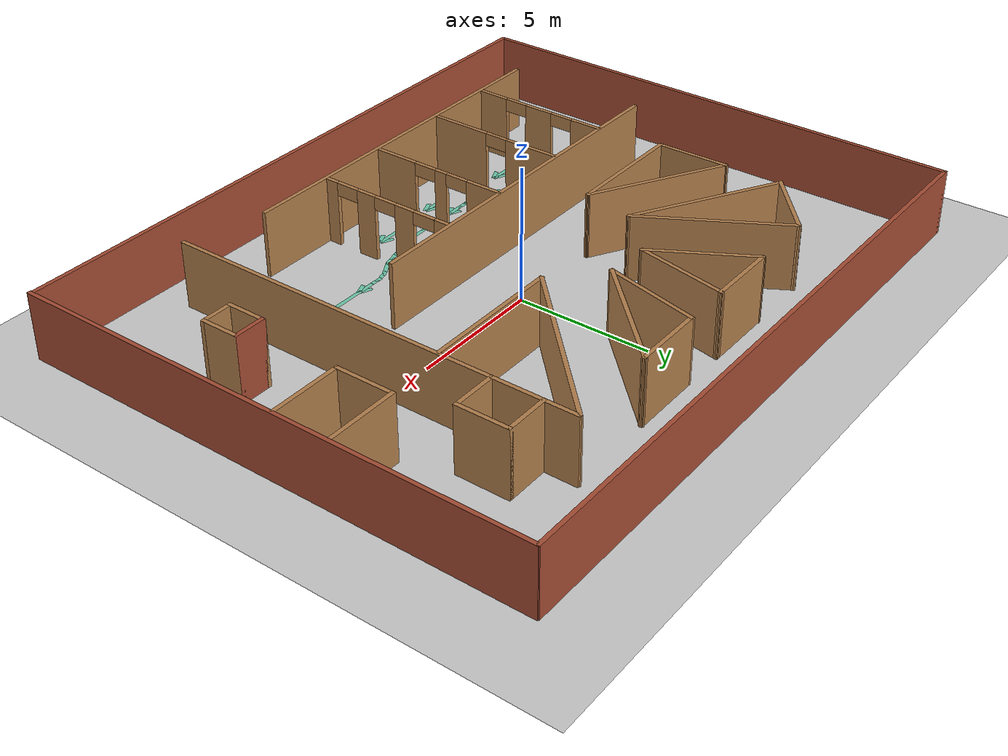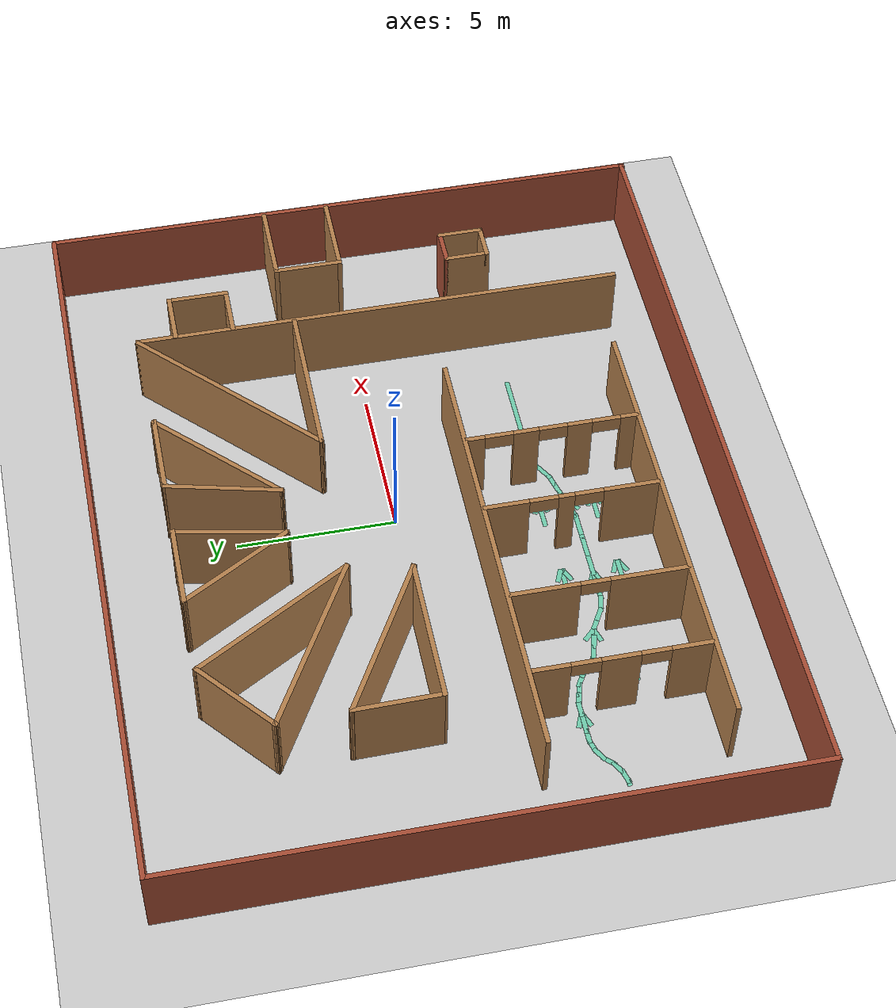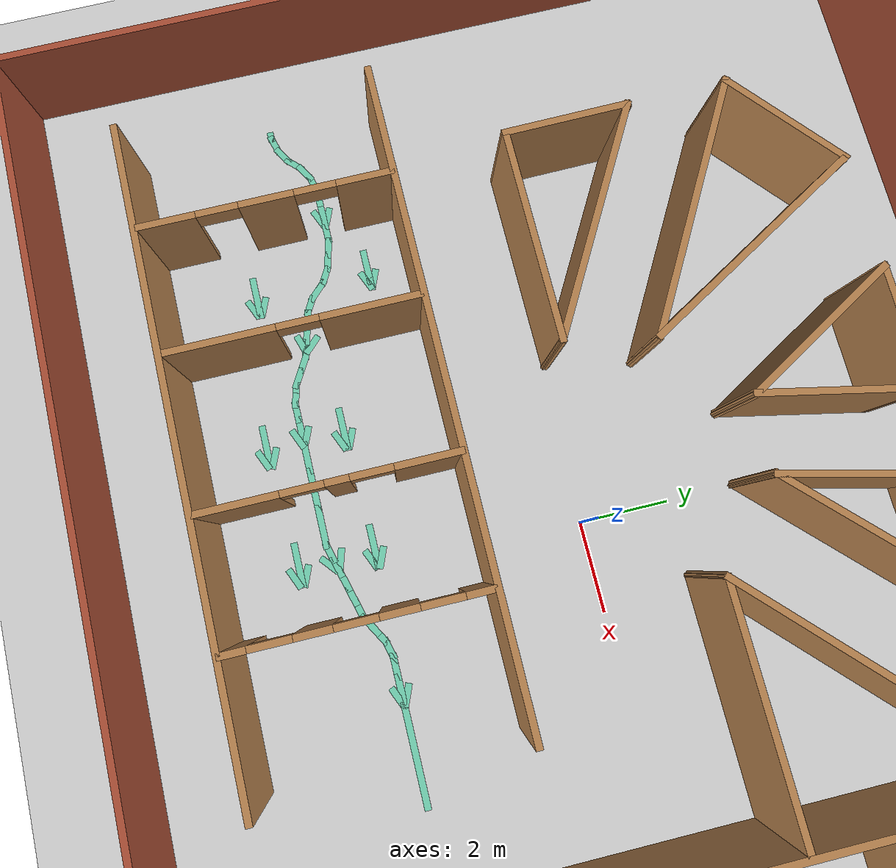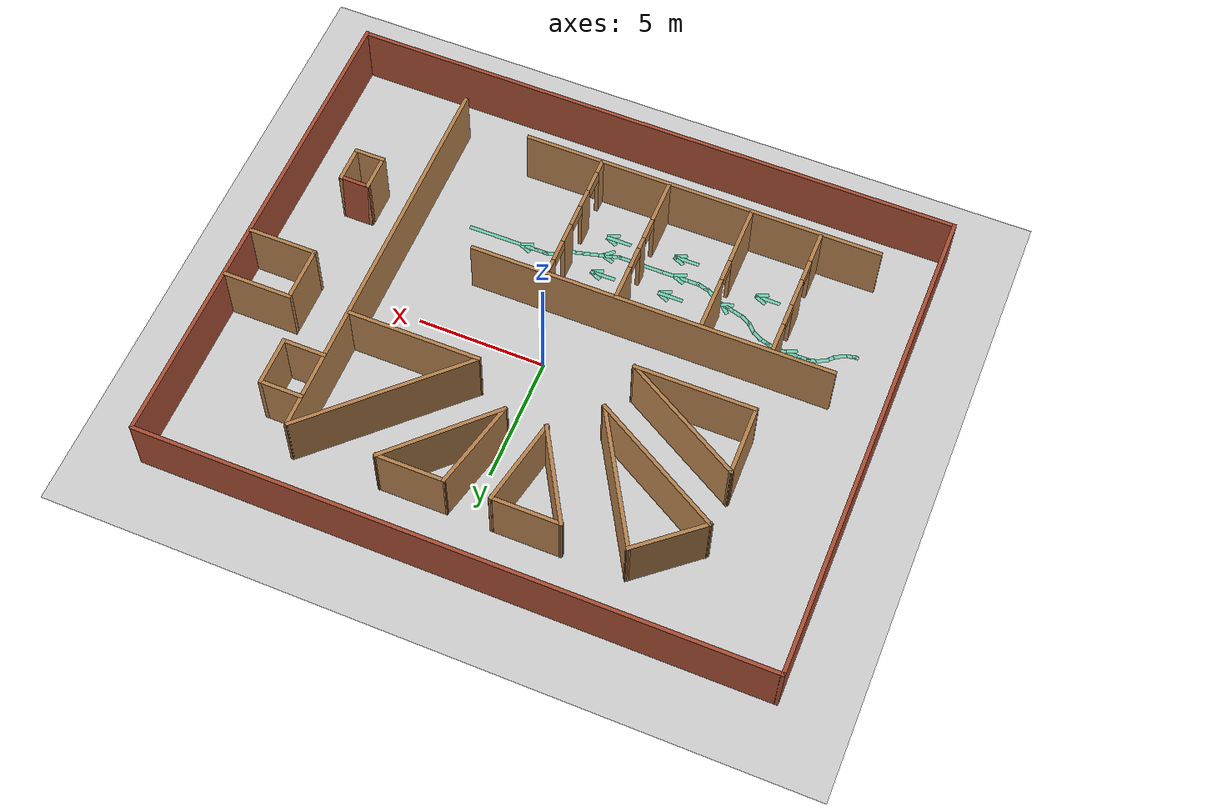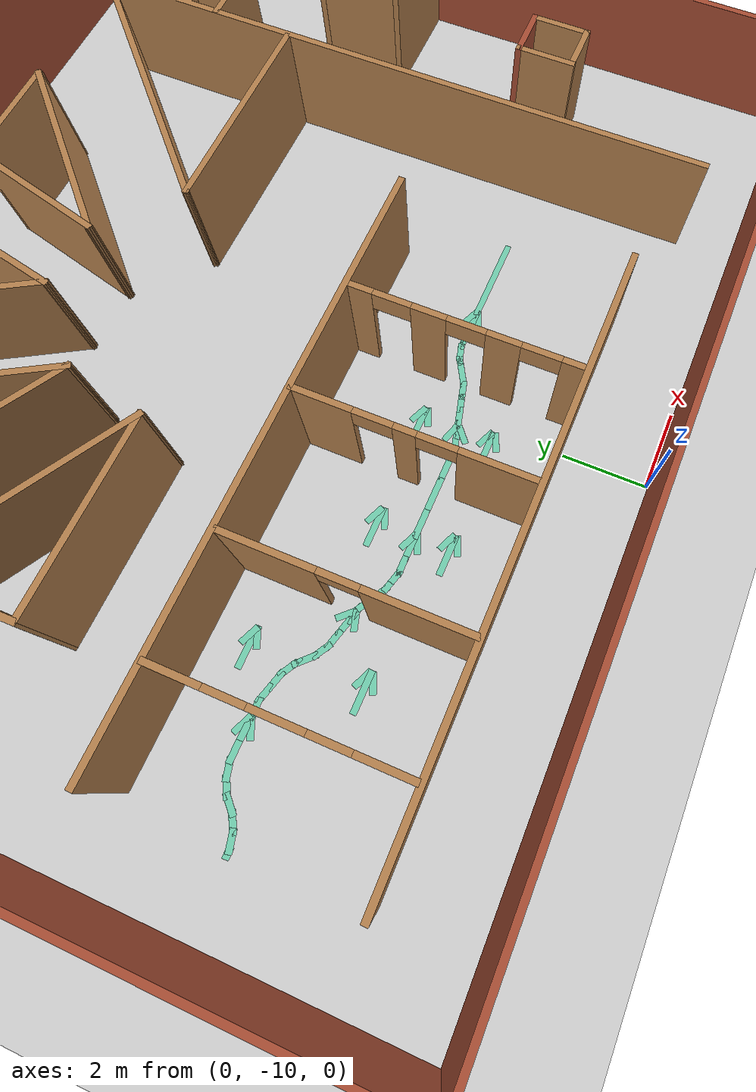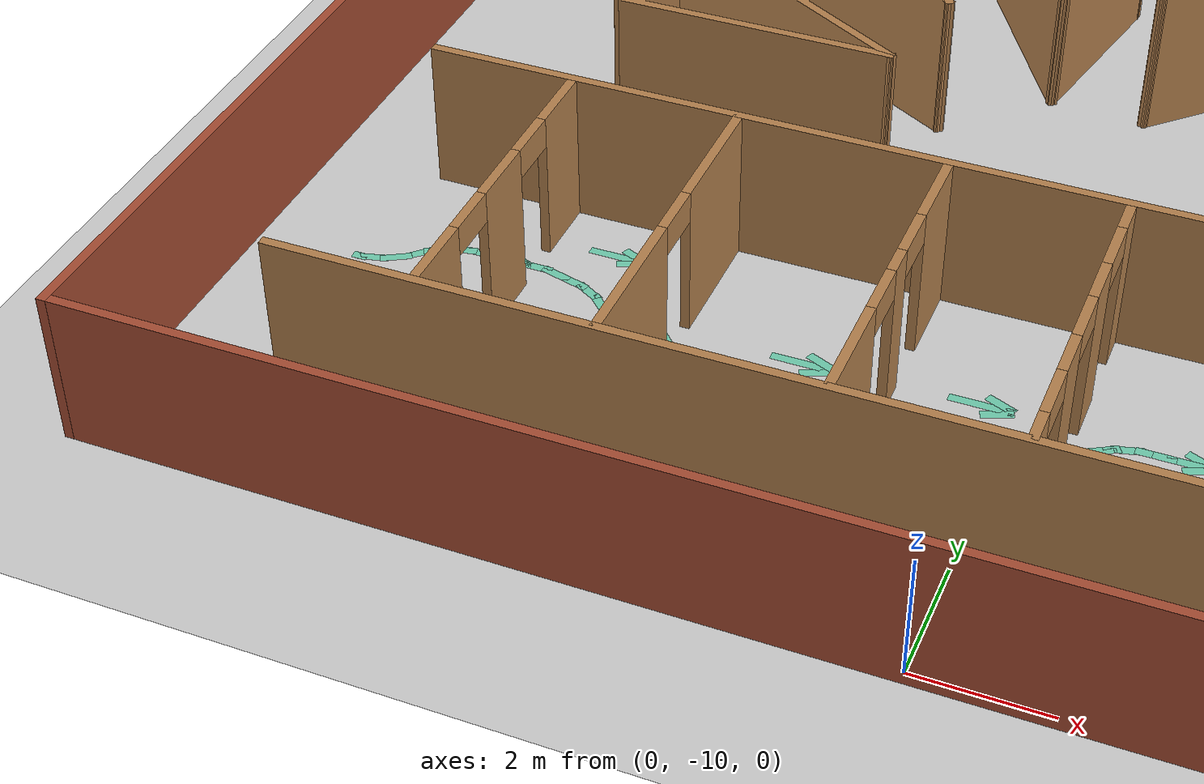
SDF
<sdf version="1.6">
 <world name="default">
  <light name="sun" type="directional">
   <pose>0 0 10 0 -0 0</pose>
   <diffuse>0.8 0.8 0.8 1</diffuse>
   <specular>0.1 0.1 0.1 1</specular>
   <attenuation>
    <range>1000</range>
    <constant>0.9</constant>
    <linear>0.01</linear>
    <quadratic>0.001</quadratic>
   </attenuation>
   <direction>-0.5 0.5 -1</direction>
  </light>
  <model name="ground_plane">
   <static>1</static>
   <link name="link">
    <collision name="collision">
     <geometry><plane><normal>0 0 1</normal><size>100 100</size></plane></geometry>
     <surface><friction><ode><mu>100</mu><mu2>50</mu2></ode></friction></surface>
    </collision>
    <visual name="visual">
     <cast_shadows>0</cast_shadows>
     <geometry><plane><normal>0 0 1</normal><size>100 100</size></plane></geometry>
     <material>
      <script><uri>file://media/materials/scripts/gazebo.material</uri><name>Gazebo/Grey</name></script>
     </material>
    </visual>
   </link>
  </model>
  <gravity>0 0 -9.8</gravity>
  <magnetic_field>6e-06 2.3e-05 -4.2e-05</magnetic_field>
  <atmosphere type="adiabatic"/>
  <physics name="default_physics" default="0" type="ode">
   <max_step_size>0.001</max_step_size>
   <real_time_factor>1</real_time_factor>
   <real_time_update_rate>1000</real_time_update_rate>
  </physics>
  <scene><ambient>0.4 0.4 0.4 1</ambient><background>0.7 0.7 0.7 1</background><shadows>1</shadows></scene>
  <spherical_coordinates>
   <surface_model>EARTH_WGS84</surface_model>
   <latitude_deg>0</latitude_deg>
   <longitude_deg>0</longitude_deg>
   <elevation>0</elevation>
   <heading_deg>0</heading_deg>
  </spherical_coordinates>
  <model name="sc_test_scenario">
   <pose>-0.29027 -0.45151 0 0 -0 0</pose>
   <link name="Wall_101">
    <pose>-7.64296 -4.61113 0 0 0 -1.5708</pose>
    <visual name="Wall_101_Visual_0">
     <pose>-2.12348 0 1.25 0 -0 0</pose>
     <geometry><box><size>1.25304 0.15 2.5</size></box></geometry>
     <material>
      <script><uri>file://media/materials/scripts/gazebo.material</uri><name>Gazebo/Wood</name></script>
      <ambient>1 1 1 1</ambient>
     </material>
    </visual>
    <collision name="Wall_101_Collision_0">
     <geometry><box><size>1.25304 0.15 2.5</size></box></geometry>
     <pose>-2.12348 0 1.25 0 -0 0</pose>
    </collision>
    <visual name="Wall_101_Visual_1">
     <pose>-0.006889 0 1.25 0 -0 0</pose>
     <geometry><box><size>1.18014 0.15 2.5</size></box></geometry>
     <material>
      <script><uri>file://media/materials/scripts/gazebo.material</uri><name>Gazebo/Wood</name></script>
      <ambient>1 1 1 1</ambient>
     </material>
    </visual>
    <collision name="Wall_101_Collision_1">
     <geometry><box><size>1.18014 0.15 2.5</size></box></geometry>
     <pose>-0.006889 0 1.25 0 -0 0</pose>
    </collision>
    <visual name="Wall_101_Visual_2">
     <pose>2.11659 0 1.25 0 -0 0</pose>
     <geometry><box><size>1.26682 0.15 2.5</size></box></geometry>
     <material>
      <script><uri>file://media/materials/scripts/gazebo.material</uri><name>Gazebo/Wood</name></script>
      <ambient>1 1 1 1</ambient>
     </material>
    </visual>
    <collision name="Wall_101_Collision_2">
     <geometry><box><size>1.26682 0.15 2.5</size></box></geometry>
     <pose>2.11659 0 1.25 0 -0 0</pose>
    </collision>
    <visual name="Wall_101_Visual_3">
     <pose>-1.04696 0 2.25 0 -0 0</pose>
     <geometry><box><size>0.9 0.15 0.5</size></box></geometry>
     <material>
      <script><uri>file://media/materials/scripts/gazebo.material</uri><name>Gazebo/Wood</name></script>
      <ambient>1 1 1 1</ambient>
     </material>
    </visual>
    <collision name="Wall_101_Collision_3">
     <geometry><box><size>0.9 0.15 0.5</size></box></geometry>
     <pose>-1.04696 0 2.25 0 -0 0</pose>
    </collision>
    <visual name="Wall_101_Visual_4">
     <pose>1.03318 0 2.25 0 -0 0</pose>
     <geometry><box><size>0.9 0.15 0.5</size></box></geometry>
     <material>
      <script><uri>file://media/materials/scripts/gazebo.material</uri><name>Gazebo/Wood</name></script>
      <ambient>1 1 1 1</ambient>
     </material>
    </visual>
    <collision name="Wall_101_Collision_4">
     <geometry><box><size>0.9 0.15 0.5</size></box></geometry>
     <pose>1.03318 0 2.25 0 -0 0</pose>
    </collision>
   </link>
   <link name="Wall_103">
    <pose>-1.59718 -4.61113 0 0 0 -1.5708</pose>
    <visual name="Wall_103_Visual_0">
     <pose>-2.03171 0 1.25 0 -0 0</pose>
     <geometry><box><size>1.43658 0.15 2.5</size></box></geometry>
     <material>
      <script><uri>file://media/materials/scripts/gazebo.material</uri><name>Gazebo/Wood</name></script>
      <ambient>1 1 1 1</ambient>
     </material>
    </visual>
    <collision name="Wall_103_Collision_0">
     <geometry><box><size>1.43658 0.15 2.5</size></box></geometry>
     <pose>-2.03171 0 1.25 0 -0 0</pose>
    </collision>
    <visual name="Wall_103_Visual_1">
     <pose>-0.15984 0 1.25 0 -0 0</pose>
     <geometry><box><size>0.507151 0.15 2.5</size></box></geometry>
     <material>
      <script><uri>file://media/materials/scripts/gazebo.material</uri><name>Gazebo/Wood</name></script>
      <ambient>1 1 1 1</ambient>
     </material>
    </visual>
    <collision name="Wall_103_Collision_1">
     <geometry><box><size>0.507151 0.15 2.5</size></box></geometry>
     <pose>-0.15984 0 1.25 0 -0 0</pose>
    </collision>
    <visual name="Wall_103_Visual_2">
     <pose>1.87187 0 1.25 0 -0 0</pose>
     <geometry><box><size>1.75626 0.15 2.5</size></box></geometry>
     <material>
      <script><uri>file://media/materials/scripts/gazebo.material</uri><name>Gazebo/Wood</name></script>
      <ambient>1 1 1 1</ambient>
     </material>
    </visual>
    <collision name="Wall_103_Collision_2">
     <geometry><box><size>1.75626 0.15 2.5</size></box></geometry>
     <pose>1.87187 0 1.25 0 -0 0</pose>
    </collision>
    <visual name="Wall_103_Visual_3">
     <pose>-0.863416 0 2.25 0 -0 0</pose>
     <geometry><box><size>0.9 0.15 0.5</size></box></geometry>
     <material>
      <script><uri>file://media/materials/scripts/gazebo.material</uri><name>Gazebo/Wood</name></script>
      <ambient>1 1 1 1</ambient>
     </material>
    </visual>
    <collision name="Wall_103_Collision_3">
     <geometry><box><size>0.9 0.15 0.5</size></box></geometry>
     <pose>-0.863416 0 2.25 0 -0 0</pose>
    </collision>
    <visual name="Wall_103_Visual_4">
     <pose>0.543735 0 2.25 0 -0 0</pose>
     <geometry><box><size>0.9 0.15 0.5</size></box></geometry>
     <material>
      <script><uri>file://media/materials/scripts/gazebo.material</uri><name>Gazebo/Wood</name></script>
      <ambient>1 1 1 1</ambient>
     </material>
    </visual>
    <collision name="Wall_103_Collision_4">
     <geometry><box><size>0.9 0.15 0.5</size></box></geometry>
     <pose>0.543735 0 2.25 0 -0 0</pose>
    </collision>
   </link>
   <link name="Wall_105">
    <collision name="Wall_105_Collision">
     <geometry><box><size>1.75 0.15 2.5</size></box></geometry>
     <pose>0 0 1.25 0 -0 0</pose>
    </collision>
    <visual name="Wall_105_Visual">
     <pose>0 0 1.25 0 -0 0</pose>
     <geometry><box><size>1.75 0.15 2.5</size></box></geometry>
     <material>
      <script><uri>file://media/materials/scripts/gazebo.material</uri><name>Gazebo/Wood</name></script>
      <ambient>1 1 1 1</ambient>
     </material>
    </visual>
    <pose>7.95828 6.28458 0 0 -0 0</pose>
   </link>
   <link name="Wall_106">
    <collision name="Wall_106_Collision">
     <geometry><box><size>2 0.15 2.5</size></box></geometry>
     <pose>0 0 1.25 0 -0 0</pose>
    </collision>
    <visual name="Wall_106_Visual">
     <pose>0 0 1.25 0 -0 0</pose>
     <geometry><box><size>2 0.15 2.5</size></box></geometry>
     <material>
      <script><uri>file://media/materials/scripts/gazebo.material</uri><name>Gazebo/Wood</name></script>
      <ambient>1 1 1 1</ambient>
     </material>
    </visual>
    <pose>8.75829 5.35958 0 0 0 -1.5708</pose>
   </link>
   <link name="Wall_107">
    <collision name="Wall_107_Collision">
     <geometry><box><size>1.75 0.15 2.5</size></box></geometry>
     <pose>0 0 1.25 0 -0 0</pose>
    </collision>
    <visual name="Wall_107_Visual">
     <pose>0 0 1.25 0 -0 0</pose>
     <geometry><box><size>1.75 0.15 2.5</size></box></geometry>
     <material>
      <script><uri>file://media/materials/scripts/gazebo.material</uri><name>Gazebo/Wood</name></script>
      <ambient>1 1 1 1</ambient>
     </material>
    </visual>
    <pose>7.95828 4.43457 0 0 -0 3.14159</pose>
   </link>
   <link name="Wall_114">
    <collision name="Wall_114_Collision">
     <geometry><box><size>2.75 0.15 2.5</size></box></geometry>
     <pose>0 0 1.25 0 -0 0</pose>
    </collision>
    <visual name="Wall_114_Visual">
     <pose>0 0 1.25 0 -0 0</pose>
     <geometry><box><size>2.75 0.15 2.5</size></box></geometry>
     <material>
      <script><uri>file://media/materials/scripts/gazebo.material</uri><name>Gazebo/Wood</name></script>
      <ambient>1 1 1 1</ambient>
     </material>
    </visual>
    <pose>10.7228 2.66437 0 0 -0 3.14159</pose>
   </link>
   <link name="Wall_115">
    <collision name="Wall_115_Collision">
     <geometry><box><size>2.25 0.15 2.5</size></box></geometry>
     <pose>0 0 1.25 0 -0 0</pose>
    </collision>
    <visual name="Wall_115_Visual">
     <pose>0 0 1.25 0 -0 0</pose>
     <geometry><box><size>2.25 0.15 2.5</size></box></geometry>
     <material>
      <script><uri>file://media/materials/scripts/gazebo.material</uri><name>Gazebo/Wood</name></script>
      <ambient>1 1 1 1</ambient>
     </material>
    </visual>
    <pose>9.42281 1.61437 0 0 0 -1.5708</pose>
   </link>
   <link name="Wall_116">
    <collision name="Wall_116_Collision">
     <geometry><box><size>2.75 0.15 2.5</size></box></geometry>
     <pose>0 0 1.25 0 -0 0</pose>
    </collision>
    <visual name="Wall_116_Visual">
     <pose>0 0 1.25 0 -0 0</pose>
     <geometry><box><size>2.75 0.15 2.5</size></box></geometry>
     <material>
      <script><uri>file://media/materials/scripts/gazebo.material</uri><name>Gazebo/Wood</name></script>
      <ambient>1 1 1 1</ambient>
     </material>
    </visual>
    <pose>10.7228 0.564366 0 0 -0 0</pose>
   </link>
   <link name="Wall_124">
    <collision name="Wall_124_Collision">
     <geometry><box><size>1.25 0.15 2.5</size></box></geometry>
     <pose>0 0 1.25 0 -0 0</pose>
    </collision>
    <visual name="Wall_124_Visual">
     <pose>0 0 1.25 0 -0 0</pose>
     <geometry><box><size>1.25 0.15 2.5</size></box></geometry>
     <material>
      <script><uri>file://media/materials/scripts/gazebo.material</uri><name>Gazebo/Bricks</name></script>
      <ambient>1 1 1 1</ambient>
     </material>
    </visual>
    <pose>9.44586 -2.92352 0 0 -0 0</pose>
   </link>
   <link name="Wall_125">
    <collision name="Wall_125_Collision">
     <geometry><box><size>1.5 0.15 2.5</size></box></geometry>
     <pose>0 0 1.25 0 -0 0</pose>
    </collision>
    <visual name="Wall_125_Visual">
     <pose>0 0 1.25 0 -0 0</pose>
     <geometry><box><size>1.5 0.15 2.5</size></box></geometry>
     <material>
      <script><uri>file://media/materials/scripts/gazebo.material</uri><name>Gazebo/Wood</name></script>
      <ambient>1 1 1 1</ambient>
     </material>
    </visual>
    <pose>9.99586 -3.59852 0 0 0 -1.5708</pose>
   </link>
   <link name="Wall_126">
    <collision name="Wall_126_Collision">
     <geometry><box><size>1.25 0.15 2.5</size></box></geometry>
     <pose>0 0 1.25 0 -0 0</pose>
    </collision>
    <visual name="Wall_126_Visual">
     <pose>0 0 1.25 0 -0 0</pose>
     <geometry><box><size>1.25 0.15 2.5</size></box></geometry>
     <material>
      <script><uri>file://media/materials/scripts/gazebo.material</uri><name>Gazebo/Wood</name></script>
      <ambient>1 1 1 1</ambient>
     </material>
    </visual>
    <pose>9.44586 -4.27352 0 0 -0 3.14159</pose>
   </link>
   <link name="Wall_128">
    <collision name="Wall_128_Collision">
     <geometry><box><size>1.5 0.15 2.5</size></box></geometry>
     <pose>0 0 1.25 0 -0 0</pose>
    </collision>
    <visual name="Wall_128_Visual">
     <pose>0 0 1.25 0 -0 0</pose>
     <geometry><box><size>1.5 0.15 2.5</size></box></geometry>
     <material>
      <script><uri>file://media/materials/scripts/gazebo.material</uri><name>Gazebo/Wood</name></script>
      <ambient>1 1 1 1</ambient>
     </material>
    </visual>
    <pose>8.89586 -3.59852 0 0 0 -1.5708</pose>
   </link>
   <link name="Wall_23">
    <collision name="Wall_23_Collision">
     <geometry><box><size>24.3217 0.15 2.5</size></box></geometry>
     <pose>0 0 1.25 0 -0 0</pose>
    </collision>
    <visual name="Wall_23_Visual">
     <pose>0 0 1.25 0 -0 0</pose>
     <geometry><box><size>24.3217 0.15 2.5</size></box></geometry>
     <material>
      <script><uri>file://media/materials/scripts/gazebo.material</uri><name>Gazebo/Bricks</name></script>
      <ambient>1 1 1 1</ambient>
     </material>
    </visual>
    <pose>-0.017586 9.69259 0 0 0 -0.000108</pose>
   </link>
   <link name="Wall_24">
    <collision name="Wall_24_Collision">
     <geometry><box><size>19.5 0.15 2.5</size></box></geometry>
     <pose>0 0 1.25 0 -0 0</pose>
    </collision>
    <visual name="Wall_24_Visual">
     <pose>0 0 1.25 0 -0 0</pose>
     <geometry><box><size>19.5 0.15 2.5</size></box></geometry>
     <material>
      <script><uri>file://media/materials/scripts/gazebo.material</uri><name>Gazebo/Bricks</name></script>
      <ambient>1 1 1 1</ambient>
     </material>
    </visual>
    <pose>12.1035 -0.018893 0 0 0 -1.5708</pose>
   </link>
   <link name="Wall_25">
    <collision name="Wall_25_Collision">
     <geometry><box><size>24.3217 0.15 2.5</size></box></geometry>
     <pose>0 0 1.25 0 -0 0</pose>
    </collision>
    <visual name="Wall_25_Visual">
     <pose>0 0 1.25 0 -0 0</pose>
     <geometry><box><size>24.3217 0.15 2.5</size></box></geometry>
     <material>
      <script><uri>file://media/materials/scripts/gazebo.material</uri><name>Gazebo/Bricks</name></script>
      <ambient>1 1 1 1</ambient>
     </material>
    </visual>
    <pose>-0.017586 -9.65741 0 0 -0 3.14148</pose>
   </link>
   <link name="Wall_26">
    <collision name="Wall_26_Collision">
     <geometry><box><size>19.5 0.15 2.5</size></box></geometry>
     <pose>0 0 1.25 0 -0 0</pose>
    </collision>
    <visual name="Wall_26_Visual">
     <pose>0 0 1.25 0 -0 0</pose>
     <geometry><box><size>19.5 0.15 2.5</size></box></geometry>
     <material>
      <script><uri>file://media/materials/scripts/gazebo.material</uri><name>Gazebo/Bricks</name></script>
      <ambient>1 1 1 1</ambient>
     </material>
    </visual>
    <pose>-12.1035 0.018886 0 0 -0 1.5708</pose>
   </link>
   <link name="Wall_29">
    <collision name="Wall_29_Collision">
     <geometry><box><size>15.75 0.15 2.5</size></box></geometry>
     <pose>0 0 1.25 0 -0 0</pose>
    </collision>
    <visual name="Wall_29_Visual">
     <pose>0 0 1.25 0 -0 0</pose>
     <geometry><box><size>15.75 0.15 2.5</size></box></geometry>
     <material>
      <script><uri>file://media/materials/scripts/gazebo.material</uri><name>Gazebo/Wood</name></script>
      <ambient>1 1 1 1</ambient>
     </material>
    </visual>
    <pose>7.14369 -0.32029 0 0 0 -1.5708</pose>
   </link>
   <link name="Wall_42">
    <collision name="Wall_42_Collision">
     <geometry><box><size>7.34172 0.15 2.5</size></box></geometry>
     <pose>0 0 1.25 0 -0 0</pose>
    </collision>
    <visual name="Wall_42_Visual">
     <pose>0 0 1.25 0 -0 0</pose>
     <geometry><box><size>7.34172 0.15 2.5</size></box></geometry>
     <material>
      <script><uri>file://media/materials/scripts/gazebo.material</uri><name>Gazebo/Wood</name></script>
      <ambient>1 1 1 1</ambient>
     </material>
    </visual>
    <pose>4.53543 4.9684 0 0 0 -2.36834</pose>
   </link>
   <link name="Wall_43">
    <collision name="Wall_43_Collision">
     <geometry><box><size>5.25 0.15 2.5</size></box></geometry>
     <pose>0 0 1.25 0 -0 0</pose>
    </collision>
    <visual name="Wall_43_Visual">
     <pose>0 0 1.25 0 -0 0</pose>
     <geometry><box><size>5.25 0.15 2.5</size></box></geometry>
     <material>
      <script><uri>file://media/materials/scripts/gazebo.material</uri><name>Gazebo/Wood</name></script>
      <ambient>1 1 1 1</ambient>
     </material>
    </visual>
    <pose>4.52386 2.44559 0 0 -0 0</pose>
   </link>
   <link name="Wall_62">
    <collision name="Wall_62_Collision">
     <geometry><box><size>5 0.15 2.5</size></box></geometry>
     <pose>0 0 1.25 0 -0 0</pose>
    </collision>
    <visual name="Wall_62_Visual">
     <pose>0 0 1.25 0 -0 0</pose>
     <geometry><box><size>5 0.15 2.5</size></box></geometry>
     <material>
      <script><uri>file://media/materials/scripts/gazebo.material</uri><name>Gazebo/Wood</name></script>
      <ambient>1 1 1 1</ambient>
     </material>
    </visual>
    <pose>1.99557 5.69381 0 0 -0 0.785398</pose>
   </link>
   <link name="Wall_63">
    <collision name="Wall_63_Collision">
     <geometry><box><size>2.75 0.15 2.5</size></box></geometry>
     <pose>0 0 1.25 0 -0 0</pose>
    </collision>
    <visual name="Wall_63_Visual">
     <pose>0 0 1.25 0 -0 0</pose>
     <geometry><box><size>2.75 0.15 2.5</size></box></geometry>
     <material>
      <script><uri>file://media/materials/scripts/gazebo.material</uri><name>Gazebo/Wood</name></script>
      <ambient>1 1 1 1</ambient>
     </material>
    </visual>
    <pose>2.41031 7.40854 0 0 -0 3.14159</pose>
   </link>
   <link name="Wall_64">
    <collision name="Wall_64_Collision">
     <geometry><box><size>3.67835 0.15 2.5</size></box></geometry>
     <pose>0 0 1.25 0 -0 0</pose>
    </collision>
    <visual name="Wall_64_Visual">
     <pose>0 0 1.25 0 -0 0</pose>
     <geometry><box><size>3.67835 0.15 2.5</size></box></geometry>
     <material>
      <script><uri>file://media/materials/scripts/gazebo.material</uri><name>Gazebo/Wood</name></script>
      <ambient>1 1 1 1</ambient>
     </material>
    </visual>
    <pose>0.695573 5.69381 0 0 0 -1.8081</pose>
   </link>
   <link name="Wall_70">
    <collision name="Wall_70_Collision">
     <geometry><box><size>3.54783 0.15 2.5</size></box></geometry>
     <pose>0 0 1.25 0 -0 0</pose>
    </collision>
    <visual name="Wall_70_Visual">
     <pose>0 0 1.25 0 -0 0</pose>
     <geometry><box><size>3.54783 0.15 2.5</size></box></geometry>
     <material>
      <script><uri>file://media/materials/scripts/gazebo.material</uri><name>Gazebo/Wood</name></script>
      <ambient>1 1 1 1</ambient>
     </material>
    </visual>
    <pose>-1.00702 5.73657 0 0 -0 1.36902</pose>
   </link>
   <link name="Wall_78">
    <collision name="Wall_78_Collision">
     <geometry><box><size>4 0.15 2.5</size></box></geometry>
     <pose>0 0 1.25 0 -0 0</pose>
    </collision>
    <visual name="Wall_78_Visual">
     <pose>0 0 1.25 0 -0 0</pose>
     <geometry><box><size>4 0.15 2.5</size></box></geometry>
     <material>
      <script><uri>file://media/materials/scripts/gazebo.material</uri><name>Gazebo/Wood</name></script>
      <ambient>1 1 1 1</ambient>
     </material>
    </visual>
    <pose>-2.31 5.73922 0 0 -0 2.0944</pose>
   </link>
   <link name="Wall_79">
    <collision name="Wall_79_Collision">
     <geometry><box><size>2.75595 0.15 2.5</size></box></geometry>
     <pose>0 0 1.25 0 -0 0</pose>
    </collision>
    <visual name="Wall_79_Visual">
     <pose>0 0 1.25 0 -0 0</pose>
     <geometry><box><size>2.75595 0.15 2.5</size></box></geometry>
     <material>
      <script><uri>file://media/materials/scripts/gazebo.material</uri><name>Gazebo/Wood</name></script>
      <ambient>1 1 1 1</ambient>
     </material>
    </visual>
    <pose>-1.96952 7.40367 0 0 0 -0.002033</pose>
   </link>
   <link name="Wall_82">
    <collision name="Wall_82_Collision">
     <geometry><box><size>5.75 0.15 2.5</size></box></geometry>
     <pose>0 0 1.25 0 -0 0</pose>
    </collision>
    <visual name="Wall_82_Visual">
     <pose>0 0 1.25 0 -0 0</pose>
     <geometry><box><size>5.75 0.15 2.5</size></box></geometry>
     <material>
      <script><uri>file://media/materials/scripts/gazebo.material</uri><name>Gazebo/Wood</name></script>
      <ambient>1 1 1 1</ambient>
     </material>
    </visual>
    <pose>-4.32931 4.9617 0 0 -0 2.0944</pose>
   </link>
   <link name="Wall_84">
    <collision name="Wall_84_Collision">
     <geometry><box><size>6 0.15 2.5</size></box></geometry>
     <pose>0 0 1.25 0 -0 0</pose>
    </collision>
    <visual name="Wall_84_Visual">
     <pose>0 0 1.25 0 -0 0</pose>
     <geometry><box><size>6 0.15 2.5</size></box></geometry>
     <material>
      <script><uri>file://media/materials/scripts/gazebo.material</uri><name>Gazebo/Wood</name></script>
      <ambient>1 1 1 1</ambient>
     </material>
    </visual>
    <pose>-5.46244 3.99933 0 0 0 -0.523599</pose>
   </link>
   <link name="Wall_87">
    <collision name="Wall_87_Collision">
     <geometry><box><size>3.1233 0.15 2.5</size></box></geometry>
     <pose>0 0 1.25 0 -0 0</pose>
    </collision>
    <visual name="Wall_87_Visual">
     <pose>0 0 1.25 0 -0 0</pose>
     <geometry><box><size>3.1233 0.15 2.5</size></box></geometry>
     <material>
      <script><uri>file://media/materials/scripts/gazebo.material</uri><name>Gazebo/Wood</name></script>
      <ambient>1 1 1 1</ambient>
     </material>
    </visual>
    <pose>-6.86243 6.4242 0 0 0 -2.4375</pose>
   </link>
   <link name="Wall_89">
    <collision name="Wall_89_Collision">
     <geometry><box><size>5.5 0.15 2.5</size></box></geometry>
     <pose>0 0 1.25 0 -0 0</pose>
    </collision>
    <visual name="Wall_89_Visual">
     <pose>0 0 1.25 0 -0 0</pose>
     <geometry><box><size>5.5 0.15 2.5</size></box></geometry>
     <material>
      <script><uri>file://media/materials/scripts/gazebo.material</uri><name>Gazebo/Wood</name></script>
      <ambient>1 1 1 1</ambient>
     </material>
    </visual>
    <pose>-5.63727 1.94371 0 0 0 -0.523599</pose>
   </link>
   <link name="Wall_90">
    <collision name="Wall_90_Collision">
     <geometry><box><size>4.75 0.15 2.5</size></box></geometry>
     <pose>0 0 1.25 0 -0 0</pose>
    </collision>
    <visual name="Wall_90_Visual">
     <pose>0 0 1.25 0 -0 0</pose>
     <geometry><box><size>4.75 0.15 2.5</size></box></geometry>
     <material>
      <script><uri>file://media/materials/scripts/gazebo.material</uri><name>Gazebo/Wood</name></script>
      <ambient>1 1 1 1</ambient>
     </material>
    </visual>
    <pose>-5.62066 0.606213 0 0 -0 3.14159</pose>
   </link>
   <link name="Wall_91">
    <collision name="Wall_91_Collision">
     <geometry><box><size>2.82521 0.15 2.5</size></box></geometry>
     <pose>0 0 1.25 0 -0 0</pose>
    </collision>
    <visual name="Wall_91_Visual">
     <pose>0 0 1.25 0 -0 0</pose>
     <geometry><box><size>2.82521 0.15 2.5</size></box></geometry>
     <material>
      <script><uri>file://media/materials/scripts/gazebo.material</uri><name>Gazebo/Wood</name></script>
      <ambient>1 1 1 1</ambient>
     </material>
    </visual>
    <pose>-7.93727 1.94371 0 0 -0 1.58322</pose>
   </link>
   <link name="Wall_94">
    <collision name="Wall_94_Collision">
     <geometry><box><size>14.25 0.15 2.5</size></box></geometry>
     <pose>0 0 1.25 0 -0 0</pose>
    </collision>
    <visual name="Wall_94_Visual">
     <pose>0 0 1.25 0 -0 0</pose>
     <geometry><box><size>14.25 0.15 2.5</size></box></geometry>
     <material>
      <script><uri>file://media/materials/scripts/gazebo.material</uri><name>Gazebo/Wood</name></script>
      <ambient>1 1 1 1</ambient>
     </material>
    </visual>
    <pose>-2.95095 -1.88294 0 0 -0 0</pose>
   </link>
   <link name="Wall_99">
    <collision name="Wall_99_Collision">
     <geometry><box><size>14.25 0.15 2.5</size></box></geometry>
     <pose>0 0 1.25 0 -0 0</pose>
    </collision>
    <visual name="Wall_99_Visual">
     <pose>0 0 1.25 0 -0 0</pose>
     <geometry><box><size>14.25 0.15 2.5</size></box></geometry>
     <material>
      <script><uri>file://media/materials/scripts/gazebo.material</uri><name>Gazebo/Wood</name></script>
      <ambient>1 1 1 1</ambient>
     </material>
    </visual>
    <pose>-2.89357 -7.39339 0 0 -0 0</pose>
   </link>
   <static>1</static>
  </model>
  <model name="Untitled1">
   <pose>0.840887 -5.10393 0 0 -0 0</pose>
   <link name="Wall_0">
    <pose>0 -0 0 0 -0 -1.5708</pose>
    <visual name="Wall_0_Visual_0">
     <pose>-2.44031 0 1.25 0 -0 0</pose>
     <geometry><box><size>0.619384 0.15 2.5</size></box></geometry>
     <material>
      <script><uri>file://media/materials/scripts/gazebo.material</uri><name>Gazebo/Wood</name></script>
      <ambient>1 1 1 1</ambient>
     </material>
     <meta><layer>0</layer></meta>
    </visual>
    <collision name="Wall_0_Collision_0">
     <geometry><box><size>0.619384 0.15 2.5</size></box></geometry>
     <pose>-2.44031 0 1.25 0 -0 0</pose>
    </collision>
    <visual name="Wall_0_Visual_1">
     <pose>-0.825789 0 1.25 0 -0 0</pose>
     <geometry><box><size>0.809654 0.15 2.5</size></box></geometry>
     <material>
      <script><uri>file://media/materials/scripts/gazebo.material</uri><name>Gazebo/Wood</name></script>
      <ambient>1 1 1 1</ambient>
     </material>
     <meta><layer>0</layer></meta>
    </visual>
    <collision name="Wall_0_Collision_1">
     <geometry><box><size>0.809654 0.15 2.5</size></box></geometry>
     <pose>-0.825789 0 1.25 0 -0 0</pose>
    </collision>
    <visual name="Wall_0_Visual_2">
     <pose>0.873808 0 1.25 0 -0 0</pose>
     <geometry><box><size>0.78954 0.15 2.5</size></box></geometry>
     <material>
      <script><uri>file://media/materials/scripts/gazebo.material</uri><name>Gazebo/Wood</name></script>
      <ambient>1 1 1 1</ambient>
     </material>
     <meta><layer>0</layer></meta>
    </visual>
    <collision name="Wall_0_Collision_2">
     <geometry><box><size>0.78954 0.15 2.5</size></box></geometry>
     <pose>0.873808 0 1.25 0 -0 0</pose>
    </collision>
    <visual name="Wall_0_Visual_3">
     <pose>2.45929 0 1.25 0 -0 0</pose>
     <geometry><box><size>0.581422 0.15 2.5</size></box></geometry>
     <material>
      <script><uri>file://media/materials/scripts/gazebo.material</uri><name>Gazebo/Wood</name></script>
      <ambient>1 1 1 1</ambient>
     </material>
     <meta><layer>0</layer></meta>
    </visual>
    <collision name="Wall_0_Collision_3">
     <geometry><box><size>0.581422 0.15 2.5</size></box></geometry>
     <pose>2.45929 0 1.25 0 -0 0</pose>
    </collision>
    <visual name="Wall_0_Visual_4">
     <pose>-1.68062 0 2.25 0 -0 0</pose>
     <geometry><box><size>0.9 0.15 0.5</size></box></geometry>
     <material>
      <script><uri>file://media/materials/scripts/gazebo.material</uri><name>Gazebo/Wood</name></script>
      <ambient>1 1 1 1</ambient>
     </material>
     <meta><layer>0</layer></meta>
    </visual>
    <collision name="Wall_0_Collision_4">
     <geometry><box><size>0.9 0.15 0.5</size></box></geometry>
     <pose>-1.68062 0 2.25 0 -0 0</pose>
    </collision>
    <visual name="Wall_0_Visual_5">
     <pose>0.029038 0 2.25 0 -0 0</pose>
     <geometry><box><size>0.9 0.15 0.5</size></box></geometry>
     <material>
      <script><uri>file://media/materials/scripts/gazebo.material</uri><name>Gazebo/Wood</name></script>
      <ambient>1 1 1 1</ambient>
     </material>
     <meta><layer>0</layer></meta>
    </visual>
    <collision name="Wall_0_Collision_5">
     <geometry><box><size>0.9 0.15 0.5</size></box></geometry>
     <pose>0.029038 0 2.25 0 -0 0</pose>
    </collision>
    <visual name="Wall_0_Visual_6">
     <pose>1.71858 0 2.25 0 -0 0</pose>
     <geometry><box><size>0.9 0.15 0.5</size></box></geometry>
     <material>
      <script><uri>file://media/materials/scripts/gazebo.material</uri><name>Gazebo/Wood</name></script>
      <ambient>1 1 1 1</ambient>
     </material>
     <meta><layer>0</layer></meta>
    </visual>
    <collision name="Wall_0_Collision_6">
     <geometry><box><size>0.9 0.15 0.5</size></box></geometry>
     <pose>1.71858 0 2.25 0 -0 0</pose>
    </collision>
   </link>
   <static>1</static>
  </model>
  <model name="Untitled">
   <pose>-5.19546 -5.10399 0 0 -0 0</pose>
   <link name="Wall_3">
    <pose>0 -0 0 0 -0 -1.5708</pose>
    <visual name="Wall_3_Visual_0">
     <pose>-1.66418 0 1.25 0 -0 0</pose>
     <geometry><box><size>2.17164 0.15 2.5</size></box></geometry>
     <material>
      <script><uri>file://media/materials/scripts/gazebo.material</uri><name>Gazebo/Wood</name></script>
      <ambient>1 1 1 1</ambient>
     </material>
     <meta><layer>0</layer></meta>
    </visual>
    <collision name="Wall_3_Collision_0">
     <geometry><box><size>2.17164 0.15 2.5</size></box></geometry>
     <pose>-1.66418 0 1.25 0 -0 0</pose>
    </collision>
    <visual name="Wall_3_Visual_1">
     <pose>1.53582 0 1.25 0 -0 0</pose>
     <geometry><box><size>2.42836 0.15 2.5</size></box></geometry>
     <material>
      <script><uri>file://media/materials/scripts/gazebo.material</uri><name>Gazebo/Wood</name></script>
      <ambient>1 1 1 1</ambient>
     </material>
     <meta><layer>0</layer></meta>
    </visual>
    <collision name="Wall_3_Collision_1">
     <geometry><box><size>2.42836 0.15 2.5</size></box></geometry>
     <pose>1.53582 0 1.25 0 -0 0</pose>
    </collision>
    <visual name="Wall_3_Visual_2">
     <pose>-0.128356 0 2.25 0 -0 0</pose>
     <geometry><box><size>0.9 0.15 0.5</size></box></geometry>
     <material>
      <script><uri>file://media/materials/scripts/gazebo.material</uri><name>Gazebo/Wood</name></script>
      <ambient>1 1 1 1</ambient>
     </material>
     <meta><layer>0</layer></meta>
    </visual>
    <collision name="Wall_3_Collision_2">
     <geometry><box><size>0.9 0.15 0.5</size></box></geometry>
     <pose>-0.128356 0 2.25 0 -0 0</pose>
    </collision>
   </link>
   <static>1</static>
  </model>
  <model name="path_test">
   <link name="Wall_15">
    <pose>-6.00524 0.7938 0 0 -0 0</pose>
    <visual name="Wall_15_Visual">
     <geometry><box><size>0.5 0.15 0</size></box></geometry>
     <material>
      <script><uri>file://media/materials/scripts/gazebo.material</uri><name>Gazebo/Grey</name></script>
      <ambient>0.435294 0.796078 0.67451 1</ambient>
      <shader type="pixel"/>
     </material>
     <meta><layer>0</layer></meta>
    </visual>
    <collision name="Wall_15_Collision">
     <geometry><box><size>0.5 0.15 0</size></box></geometry>
     <surface>
      <friction>
       <ode><mu>1</mu><mu2>1</mu2><fdir1>0 0 0</fdir1><slip1>0</slip1><slip2>0</slip2></ode>
       <torsional>
        <coefficient>1</coefficient>
        <patch_radius>0</patch_radius>
        <surface_radius>0</surface_radius>
        <use_patch_radius>1</use_patch_radius>
        <ode><slip>0</slip></ode>
       </torsional>
      </friction>
      <bounce><restitution_coefficient>0</restitution_coefficient><threshold>1e+06</threshold></bounce>
      <contact>
       <collide_without_contact>0</collide_without_contact>
       <collide_without_contact_bitmask>1</collide_without_contact_bitmask>
       <collide_bitmask>1</collide_bitmask>
       <ode>
        <soft_cfm>0</soft_cfm>
        <soft_erp>0.2</soft_erp>
        <kp>1e+13</kp>
        <kd>1</kd>
        <max_vel>0.01</max_vel>
        <min_depth>0</min_depth>
       </ode>
       <bullet>
        <split_impulse>1</split_impulse>
        <split_impulse_penetration_threshold>-0.01</split_impulse_penetration_threshold>
        <soft_cfm>0</soft_cfm>
        <soft_erp>0.2</soft_erp>
        <kp>1e+13</kp>
        <kd>1</kd>
       </bullet>
      </contact>
     </surface>
    </collision>
   </link>
   <link name="Wall_16">
    <pose>-5.53024 0.7938 0 0 -0 0</pose>
    <visual name="Wall_16_Visual">
     <geometry><box><size>0.75 0.15 0</size></box></geometry>
     <material>
      <script><uri>file://media/materials/scripts/gazebo.material</uri><name>Gazebo/Grey</name></script>
      <ambient>0.435294 0.796078 0.67451 1</ambient>
      <shader type="pixel"/>
     </material>
     <meta><layer>0</layer></meta>
    </visual>
    <collision name="Wall_16_Collision">
     <geometry><box><size>0.75 0.15 0</size></box></geometry>
     <surface>
      <friction>
       <ode><mu>1</mu><mu2>1</mu2><fdir1>0 0 0</fdir1><slip1>0</slip1><slip2>0</slip2></ode>
       <torsional>
        <coefficient>1</coefficient>
        <patch_radius>0</patch_radius>
        <surface_radius>0</surface_radius>
        <use_patch_radius>1</use_patch_radius>
        <ode><slip>0</slip></ode>
       </torsional>
      </friction>
      <bounce><restitution_coefficient>0</restitution_coefficient><threshold>1e+06</threshold></bounce>
      <contact>
       <collide_without_contact>0</collide_without_contact>
       <collide_without_contact_bitmask>1</collide_without_contact_bitmask>
       <collide_bitmask>1</collide_bitmask>
       <ode>
        <soft_cfm>0</soft_cfm>
        <soft_erp>0.2</soft_erp>
        <kp>1e+13</kp>
        <kd>1</kd>
        <max_vel>0.01</max_vel>
        <min_depth>0</min_depth>
       </ode>
       <bullet>
        <split_impulse>1</split_impulse>
        <split_impulse_penetration_threshold>-0.01</split_impulse_penetration_threshold>
        <soft_cfm>0</soft_cfm>
        <soft_erp>0.2</soft_erp>
        <kp>1e+13</kp>
        <kd>1</kd>
       </bullet>
      </contact>
     </surface>
    </collision>
   </link>
   <link name="Wall_17">
    <pose>-5.05524 0.7938 0 0 -0 0</pose>
    <visual name="Wall_17_Visual">
     <geometry><box><size>0.5 0.15 0</size></box></geometry>
     <material>
      <script><uri>file://media/materials/scripts/gazebo.material</uri><name>Gazebo/Grey</name></script>
      <ambient>0.435294 0.796078 0.67451 1</ambient>
      <shader type="pixel"/>
     </material>
     <meta><layer>0</layer></meta>
    </visual>
    <collision name="Wall_17_Collision">
     <geometry><box><size>0.5 0.15 0</size></box></geometry>
     <surface>
      <friction>
       <ode><mu>1</mu><mu2>1</mu2><fdir1>0 0 0</fdir1><slip1>0</slip1><slip2>0</slip2></ode>
       <torsional>
        <coefficient>1</coefficient>
        <patch_radius>0</patch_radius>
        <surface_radius>0</surface_radius>
        <use_patch_radius>1</use_patch_radius>
        <ode><slip>0</slip></ode>
       </torsional>
      </friction>
      <bounce><restitution_coefficient>0</restitution_coefficient><threshold>1e+06</threshold></bounce>
      <contact>
       <collide_without_contact>0</collide_without_contact>
       <collide_without_contact_bitmask>1</collide_without_contact_bitmask>
       <collide_bitmask>1</collide_bitmask>
       <ode>
        <soft_cfm>0</soft_cfm>
        <soft_erp>0.2</soft_erp>
        <kp>1e+13</kp>
        <kd>1</kd>
        <max_vel>0.01</max_vel>
        <min_depth>0</min_depth>
       </ode>
       <bullet>
        <split_impulse>1</split_impulse>
        <split_impulse_penetration_threshold>-0.01</split_impulse_penetration_threshold>
        <soft_cfm>0</soft_cfm>
        <soft_erp>0.2</soft_erp>
        <kp>1e+13</kp>
        <kd>1</kd>
       </bullet>
      </contact>
     </surface>
    </collision>
   </link>
   <link name="Wall_18">
    <pose>-4.7112 0.748507 0 0 0 -0.261799</pose>
    <visual name="Wall_18_Visual">
     <geometry><box><size>0.5 0.15 0</size></box></geometry>
     <material>
      <script><uri>file://media/materials/scripts/gazebo.material</uri><name>Gazebo/Grey</name></script>
      <ambient>0.435294 0.796078 0.67451 1</ambient>
      <shader type="pixel"/>
     </material>
     <meta><layer>0</layer></meta>
    </visual>
    <collision name="Wall_18_Collision">
     <geometry><box><size>0.5 0.15 0</size></box></geometry>
     <surface>
      <friction>
       <ode><mu>1</mu><mu2>1</mu2><fdir1>0 0 0</fdir1><slip1>0</slip1><slip2>0</slip2></ode>
       <torsional>
        <coefficient>1</coefficient>
        <patch_radius>0</patch_radius>
        <surface_radius>0</surface_radius>
        <use_patch_radius>1</use_patch_radius>
        <ode><slip>0</slip></ode>
       </torsional>
      </friction>
      <bounce><restitution_coefficient>0</restitution_coefficient><threshold>1e+06</threshold></bounce>
      <contact>
       <collide_without_contact>0</collide_without_contact>
       <collide_without_contact_bitmask>1</collide_without_contact_bitmask>
       <collide_bitmask>1</collide_bitmask>
       <ode>
        <soft_cfm>0</soft_cfm>
        <soft_erp>0.2</soft_erp>
        <kp>1e+13</kp>
        <kd>1</kd>
        <max_vel>0.01</max_vel>
        <min_depth>0</min_depth>
       </ode>
       <bullet>
        <split_impulse>1</split_impulse>
        <split_impulse_penetration_threshold>-0.01</split_impulse_penetration_threshold>
        <soft_cfm>0</soft_cfm>
        <soft_erp>0.2</soft_erp>
        <kp>1e+13</kp>
        <kd>1</kd>
       </bullet>
      </contact>
     </surface>
    </collision>
   </link>
   <link name="Wall_19">
    <pose>-4.37313 0.65792 0 0 0 -0.261799</pose>
    <visual name="Wall_19_Visual">
     <geometry><box><size>0.5 0.15 0</size></box></geometry>
     <material>
      <script><uri>file://media/materials/scripts/gazebo.material</uri><name>Gazebo/Grey</name></script>
      <ambient>0.435294 0.796078 0.67451 1</ambient>
      <shader type="pixel"/>
     </material>
     <meta><layer>0</layer></meta>
    </visual>
    <collision name="Wall_19_Collision">
     <geometry><box><size>0.5 0.15 0</size></box></geometry>
     <surface>
      <friction>
       <ode><mu>1</mu><mu2>1</mu2><fdir1>0 0 0</fdir1><slip1>0</slip1><slip2>0</slip2></ode>
       <torsional>
        <coefficient>1</coefficient>
        <patch_radius>0</patch_radius>
        <surface_radius>0</surface_radius>
        <use_patch_radius>1</use_patch_radius>
        <ode><slip>0</slip></ode>
       </torsional>
      </friction>
      <bounce><restitution_coefficient>0</restitution_coefficient><threshold>1e+06</threshold></bounce>
      <contact>
       <collide_without_contact>0</collide_without_contact>
       <collide_without_contact_bitmask>1</collide_without_contact_bitmask>
       <collide_bitmask>1</collide_bitmask>
       <ode>
        <soft_cfm>0</soft_cfm>
        <soft_erp>0.2</soft_erp>
        <kp>1e+13</kp>
        <kd>1</kd>
        <max_vel>0.01</max_vel>
        <min_depth>0</min_depth>
       </ode>
       <bullet>
        <split_impulse>1</split_impulse>
        <split_impulse_penetration_threshold>-0.01</split_impulse_penetration_threshold>
        <soft_cfm>0</soft_cfm>
        <soft_erp>0.2</soft_erp>
        <kp>1e+13</kp>
        <kd>1</kd>
       </bullet>
      </contact>
     </surface>
    </collision>
   </link>
   <link name="Wall_20">
    <pose>-4.05254 0.525126 0 0 0 -0.523599</pose>
    <visual name="Wall_20_Visual">
     <geometry><box><size>0.5 0.15 0</size></box></geometry>
     <material>
      <script><uri>file://media/materials/scripts/gazebo.material</uri><name>Gazebo/Grey</name></script>
      <ambient>0.435294 0.796078 0.67451 1</ambient>
      <shader type="pixel"/>
     </material>
     <meta><layer>0</layer></meta>
    </visual>
    <collision name="Wall_20_Collision">
     <geometry><box><size>0.5 0.15 0</size></box></geometry>
     <surface>
      <friction>
       <ode><mu>1</mu><mu2>1</mu2><fdir1>0 0 0</fdir1><slip1>0</slip1><slip2>0</slip2></ode>
       <torsional>
        <coefficient>1</coefficient>
        <patch_radius>0</patch_radius>
        <surface_radius>0</surface_radius>
        <use_patch_radius>1</use_patch_radius>
        <ode><slip>0</slip></ode>
       </torsional>
      </friction>
      <bounce><restitution_coefficient>0</restitution_coefficient><threshold>1e+06</threshold></bounce>
      <contact>
       <collide_without_contact>0</collide_without_contact>
       <collide_without_contact_bitmask>1</collide_without_contact_bitmask>
       <collide_bitmask>1</collide_bitmask>
       <ode>
        <soft_cfm>0</soft_cfm>
        <soft_erp>0.2</soft_erp>
        <kp>1e+13</kp>
        <kd>1</kd>
        <max_vel>0.01</max_vel>
        <min_depth>0</min_depth>
       </ode>
       <bullet>
        <split_impulse>1</split_impulse>
        <split_impulse_penetration_threshold>-0.01</split_impulse_penetration_threshold>
        <soft_cfm>0</soft_cfm>
        <soft_erp>0.2</soft_erp>
        <kp>1e+13</kp>
        <kd>1</kd>
       </bullet>
      </contact>
     </surface>
    </collision>
   </link>
   <link name="Wall_21">
    <pose>-3.86563 0.402271 0 0 0 -0.785398</pose>
    <visual name="Wall_21_Visual">
     <geometry><box><size>0.25 0.15 0</size></box></geometry>
     <material>
      <script><uri>file://media/materials/scripts/gazebo.material</uri><name>Gazebo/Grey</name></script>
      <ambient>0.435294 0.796078 0.67451 1</ambient>
      <shader type="pixel"/>
     </material>
     <meta><layer>0</layer></meta>
    </visual>
    <collision name="Wall_21_Collision">
     <geometry><box><size>0.25 0.15 0</size></box></geometry>
     <surface>
      <friction>
       <ode><mu>1</mu><mu2>1</mu2><fdir1>0 0 0</fdir1><slip1>0</slip1><slip2>0</slip2></ode>
       <torsional>
        <coefficient>1</coefficient>
        <patch_radius>0</patch_radius>
        <surface_radius>0</surface_radius>
        <use_patch_radius>1</use_patch_radius>
        <ode><slip>0</slip></ode>
       </torsional>
      </friction>
      <bounce><restitution_coefficient>0</restitution_coefficient><threshold>1e+06</threshold></bounce>
      <contact>
       <collide_without_contact>0</collide_without_contact>
       <collide_without_contact_bitmask>1</collide_without_contact_bitmask>
       <collide_bitmask>1</collide_bitmask>
       <ode>
        <soft_cfm>0</soft_cfm>
        <soft_erp>0.2</soft_erp>
        <kp>1e+13</kp>
        <kd>1</kd>
        <max_vel>0.01</max_vel>
        <min_depth>0</min_depth>
       </ode>
       <bullet>
        <split_impulse>1</split_impulse>
        <split_impulse_penetration_threshold>-0.01</split_impulse_penetration_threshold>
        <soft_cfm>0</soft_cfm>
        <soft_erp>0.2</soft_erp>
        <kp>1e+13</kp>
        <kd>1</kd>
       </bullet>
      </contact>
     </surface>
    </collision>
   </link>
   <link name="Wall_22">
    <pose>-3.70653 0.243172 0 0 0 -0.785398</pose>
    <visual name="Wall_22_Visual">
     <geometry><box><size>0.5 0.15 0</size></box></geometry>
     <material>
      <script><uri>file://media/materials/scripts/gazebo.material</uri><name>Gazebo/Grey</name></script>
      <ambient>0.435294 0.796078 0.67451 1</ambient>
      <shader type="pixel"/>
     </material>
     <meta><layer>0</layer></meta>
    </visual>
    <collision name="Wall_22_Collision">
     <geometry><box><size>0.5 0.15 0</size></box></geometry>
     <surface>
      <friction>
       <ode><mu>1</mu><mu2>1</mu2><fdir1>0 0 0</fdir1><slip1>0</slip1><slip2>0</slip2></ode>
       <torsional>
        <coefficient>1</coefficient>
        <patch_radius>0</patch_radius>
        <surface_radius>0</surface_radius>
        <use_patch_radius>1</use_patch_radius>
        <ode><slip>0</slip></ode>
       </torsional>
      </friction>
      <bounce><restitution_coefficient>0</restitution_coefficient><threshold>1e+06</threshold></bounce>
      <contact>
       <collide_without_contact>0</collide_without_contact>
       <collide_without_contact_bitmask>1</collide_without_contact_bitmask>
       <collide_bitmask>1</collide_bitmask>
       <ode>
        <soft_cfm>0</soft_cfm>
        <soft_erp>0.2</soft_erp>
        <kp>1e+13</kp>
        <kd>1</kd>
        <max_vel>0.01</max_vel>
        <min_depth>0</min_depth>
       </ode>
       <bullet>
        <split_impulse>1</split_impulse>
        <split_impulse_penetration_threshold>-0.01</split_impulse_penetration_threshold>
        <soft_cfm>0</soft_cfm>
        <soft_erp>0.2</soft_erp>
        <kp>1e+13</kp>
        <kd>1</kd>
       </bullet>
      </contact>
     </surface>
    </collision>
   </link>
   <link name="Wall_23">
    <pose>-3.43123 0.031929 0 0 0 -0.523599</pose>
    <visual name="Wall_23_Visual">
     <geometry><box><size>0.5 0.15 0</size></box></geometry>
     <material>
      <script><uri>file://media/materials/scripts/gazebo.material</uri><name>Gazebo/Grey</name></script>
      <ambient>0.435294 0.796078 0.67451 1</ambient>
      <shader type="pixel"/>
     </material>
     <meta><layer>0</layer></meta>
    </visual>
    <collision name="Wall_23_Collision">
     <geometry><box><size>0.5 0.15 0</size></box></geometry>
     <surface>
      <friction>
       <ode><mu>1</mu><mu2>1</mu2><fdir1>0 0 0</fdir1><slip1>0</slip1><slip2>0</slip2></ode>
       <torsional>
        <coefficient>1</coefficient>
        <patch_radius>0</patch_radius>
        <surface_radius>0</surface_radius>
        <use_patch_radius>1</use_patch_radius>
        <ode><slip>0</slip></ode>
       </torsional>
      </friction>
      <bounce><restitution_coefficient>0</restitution_coefficient><threshold>1e+06</threshold></bounce>
      <contact>
       <collide_without_contact>0</collide_without_contact>
       <collide_without_contact_bitmask>1</collide_without_contact_bitmask>
       <collide_bitmask>1</collide_bitmask>
       <ode>
        <soft_cfm>0</soft_cfm>
        <soft_erp>0.2</soft_erp>
        <kp>1e+13</kp>
        <kd>1</kd>
        <max_vel>0.01</max_vel>
        <min_depth>0</min_depth>
       </ode>
       <bullet>
        <split_impulse>1</split_impulse>
        <split_impulse_penetration_threshold>-0.01</split_impulse_penetration_threshold>
        <soft_cfm>0</soft_cfm>
        <soft_erp>0.2</soft_erp>
        <kp>1e+13</kp>
        <kd>1</kd>
       </bullet>
      </contact>
     </surface>
    </collision>
   </link>
   <link name="Wall_24">
    <pose>-3.11064 -0.100865 0 0 0 -0.261799</pose>
    <visual name="Wall_24_Visual">
     <geometry><box><size>0.5 0.15 0</size></box></geometry>
     <material>
      <script><uri>file://media/materials/scripts/gazebo.material</uri><name>Gazebo/Grey</name></script>
      <ambient>0.435294 0.796078 0.67451 1</ambient>
      <shader type="pixel"/>
     </material>
     <meta><layer>0</layer></meta>
    </visual>
    <collision name="Wall_24_Collision">
     <geometry><box><size>0.5 0.15 0</size></box></geometry>
     <surface>
      <friction>
       <ode><mu>1</mu><mu2>1</mu2><fdir1>0 0 0</fdir1><slip1>0</slip1><slip2>0</slip2></ode>
       <torsional>
        <coefficient>1</coefficient>
        <patch_radius>0</patch_radius>
        <surface_radius>0</surface_radius>
        <use_patch_radius>1</use_patch_radius>
        <ode><slip>0</slip></ode>
       </torsional>
      </friction>
      <bounce><restitution_coefficient>0</restitution_coefficient><threshold>1e+06</threshold></bounce>
      <contact>
       <collide_without_contact>0</collide_without_contact>
       <collide_without_contact_bitmask>1</collide_without_contact_bitmask>
       <collide_bitmask>1</collide_bitmask>
       <ode>
        <soft_cfm>0</soft_cfm>
        <soft_erp>0.2</soft_erp>
        <kp>1e+13</kp>
        <kd>1</kd>
        <max_vel>0.01</max_vel>
        <min_depth>0</min_depth>
       </ode>
       <bullet>
        <split_impulse>1</split_impulse>
        <split_impulse_penetration_threshold>-0.01</split_impulse_penetration_threshold>
        <soft_cfm>0</soft_cfm>
        <soft_erp>0.2</soft_erp>
        <kp>1e+13</kp>
        <kd>1</kd>
       </bullet>
      </contact>
     </surface>
    </collision>
   </link>
   <link name="Wall_25">
    <pose>-2.77256 -0.191452 0 0 0 -0.261799</pose>
    <visual name="Wall_25_Visual">
     <geometry><box><size>0.5 0.15 0</size></box></geometry>
     <material>
      <script><uri>file://media/materials/scripts/gazebo.material</uri><name>Gazebo/Grey</name></script>
      <ambient>0.435294 0.796078 0.67451 1</ambient>
      <shader type="pixel"/>
     </material>
     <meta><layer>0</layer></meta>
    </visual>
    <collision name="Wall_25_Collision">
     <geometry><box><size>0.5 0.15 0</size></box></geometry>
     <surface>
      <friction>
       <ode><mu>1</mu><mu2>1</mu2><fdir1>0 0 0</fdir1><slip1>0</slip1><slip2>0</slip2></ode>
       <torsional>
        <coefficient>1</coefficient>
        <patch_radius>0</patch_radius>
        <surface_radius>0</surface_radius>
        <use_patch_radius>1</use_patch_radius>
        <ode><slip>0</slip></ode>
       </torsional>
      </friction>
      <bounce><restitution_coefficient>0</restitution_coefficient><threshold>1e+06</threshold></bounce>
      <contact>
       <collide_without_contact>0</collide_without_contact>
       <collide_without_contact_bitmask>1</collide_without_contact_bitmask>
       <collide_bitmask>1</collide_bitmask>
       <ode>
        <soft_cfm>0</soft_cfm>
        <soft_erp>0.2</soft_erp>
        <kp>1e+13</kp>
        <kd>1</kd>
        <max_vel>0.01</max_vel>
        <min_depth>0</min_depth>
       </ode>
       <bullet>
        <split_impulse>1</split_impulse>
        <split_impulse_penetration_threshold>-0.01</split_impulse_penetration_threshold>
        <soft_cfm>0</soft_cfm>
        <soft_erp>0.2</soft_erp>
        <kp>1e+13</kp>
        <kd>1</kd>
       </bullet>
      </contact>
     </surface>
    </collision>
   </link>
   <link name="Wall_27">
    <pose>-2.1139 -0.414832 0 0 0 -0.523599</pose>
    <visual name="Wall_27_Visual">
     <geometry><box><size>0.5 0.15 0</size></box></geometry>
     <material>
      <script><uri>file://media/materials/scripts/gazebo.material</uri><name>Gazebo/Grey</name></script>
      <ambient>0.435294 0.796078 0.67451 1</ambient>
      <shader type="pixel"/>
     </material>
     <meta><layer>0</layer></meta>
    </visual>
    <collision name="Wall_27_Collision">
     <geometry><box><size>0.5 0.15 0</size></box></geometry>
     <surface>
      <friction>
       <ode><mu>1</mu><mu2>1</mu2><fdir1>0 0 0</fdir1><slip1>0</slip1><slip2>0</slip2></ode>
       <torsional>
        <coefficient>1</coefficient>
        <patch_radius>0</patch_radius>
        <surface_radius>0</surface_radius>
        <use_patch_radius>1</use_patch_radius>
        <ode><slip>0</slip></ode>
       </torsional>
      </friction>
      <bounce><restitution_coefficient>0</restitution_coefficient><threshold>1e+06</threshold></bounce>
      <contact>
       <collide_without_contact>0</collide_without_contact>
       <collide_without_contact_bitmask>1</collide_without_contact_bitmask>
       <collide_bitmask>1</collide_bitmask>
       <ode>
        <soft_cfm>0</soft_cfm>
        <soft_erp>0.2</soft_erp>
        <kp>1e+13</kp>
        <kd>1</kd>
        <max_vel>0.01</max_vel>
        <min_depth>0</min_depth>
       </ode>
       <bullet>
        <split_impulse>1</split_impulse>
        <split_impulse_penetration_threshold>-0.01</split_impulse_penetration_threshold>
        <soft_cfm>0</soft_cfm>
        <soft_erp>0.2</soft_erp>
        <kp>1e+13</kp>
        <kd>1</kd>
       </bullet>
      </contact>
     </surface>
    </collision>
   </link>
   <link name="Wall_28">
    <pose>-1.81079 -0.589831 0 0 0 -0.523599</pose>
    <visual name="Wall_28_Visual">
     <geometry><box><size>0.5 0.15 0</size></box></geometry>
     <material>
      <script><uri>file://media/materials/scripts/gazebo.material</uri><name>Gazebo/Grey</name></script>
      <ambient>0.435294 0.796078 0.67451 1</ambient>
      <shader type="pixel"/>
     </material>
     <meta><layer>0</layer></meta>
    </visual>
    <collision name="Wall_28_Collision">
     <geometry><box><size>0.5 0.15 0</size></box></geometry>
     <surface>
      <friction>
       <ode><mu>1</mu><mu2>1</mu2><fdir1>0 0 0</fdir1><slip1>0</slip1><slip2>0</slip2></ode>
       <torsional>
        <coefficient>1</coefficient>
        <patch_radius>0</patch_radius>
        <surface_radius>0</surface_radius>
        <use_patch_radius>1</use_patch_radius>
        <ode><slip>0</slip></ode>
       </torsional>
      </friction>
      <bounce><restitution_coefficient>0</restitution_coefficient><threshold>1e+06</threshold></bounce>
      <contact>
       <collide_without_contact>0</collide_without_contact>
       <collide_without_contact_bitmask>1</collide_without_contact_bitmask>
       <collide_bitmask>1</collide_bitmask>
       <ode>
        <soft_cfm>0</soft_cfm>
        <soft_erp>0.2</soft_erp>
        <kp>1e+13</kp>
        <kd>1</kd>
        <max_vel>0.01</max_vel>
        <min_depth>0</min_depth>
       </ode>
       <bullet>
        <split_impulse>1</split_impulse>
        <split_impulse_penetration_threshold>-0.01</split_impulse_penetration_threshold>
        <soft_cfm>0</soft_cfm>
        <soft_erp>0.2</soft_erp>
        <kp>1e+13</kp>
        <kd>1</kd>
       </bullet>
      </contact>
     </surface>
    </collision>
   </link>
   <link name="Wall_29">
    <pose>-1.61094 -0.690272 0 0 0 -0.261799</pose>
    <visual name="Wall_29_Visual">
     <geometry><box><size>0.25 0.15 0</size></box></geometry>
     <material>
      <script><uri>file://media/materials/scripts/gazebo.material</uri><name>Gazebo/Grey</name></script>
      <ambient>0.435294 0.796078 0.67451 1</ambient>
      <shader type="pixel"/>
     </material>
     <meta><layer>0</layer></meta>
    </visual>
    <collision name="Wall_29_Collision">
     <geometry><box><size>0.25 0.15 0</size></box></geometry>
     <surface>
      <friction>
       <ode><mu>1</mu><mu2>1</mu2><fdir1>0 0 0</fdir1><slip1>0</slip1><slip2>0</slip2></ode>
       <torsional>
        <coefficient>1</coefficient>
        <patch_radius>0</patch_radius>
        <surface_radius>0</surface_radius>
        <use_patch_radius>1</use_patch_radius>
        <ode><slip>0</slip></ode>
       </torsional>
      </friction>
      <bounce><restitution_coefficient>0</restitution_coefficient><threshold>1e+06</threshold></bounce>
      <contact>
       <collide_without_contact>0</collide_without_contact>
       <collide_without_contact_bitmask>1</collide_without_contact_bitmask>
       <collide_bitmask>1</collide_bitmask>
       <ode>
        <soft_cfm>0</soft_cfm>
        <soft_erp>0.2</soft_erp>
        <kp>1e+13</kp>
        <kd>1</kd>
        <max_vel>0.01</max_vel>
        <min_depth>0</min_depth>
       </ode>
       <bullet>
        <split_impulse>1</split_impulse>
        <split_impulse_penetration_threshold>-0.01</split_impulse_penetration_threshold>
        <soft_cfm>0</soft_cfm>
        <soft_erp>0.2</soft_erp>
        <kp>1e+13</kp>
        <kd>1</kd>
       </bullet>
      </contact>
     </surface>
    </collision>
   </link>
   <link name="Wall_30">
    <pose>-1.39361 -0.748507 0 0 0 -0.261799</pose>
    <visual name="Wall_30_Visual">
     <geometry><box><size>0.5 0.15 0</size></box></geometry>
     <material>
      <script><uri>file://media/materials/scripts/gazebo.material</uri><name>Gazebo/Grey</name></script>
      <ambient>0.435294 0.796078 0.67451 1</ambient>
      <shader type="pixel"/>
     </material>
     <meta><layer>0</layer></meta>
    </visual>
    <collision name="Wall_30_Collision">
     <geometry><box><size>0.5 0.15 0</size></box></geometry>
     <surface>
      <friction>
       <ode><mu>1</mu><mu2>1</mu2><fdir1>0 0 0</fdir1><slip1>0</slip1><slip2>0</slip2></ode>
       <torsional>
        <coefficient>1</coefficient>
        <patch_radius>0</patch_radius>
        <surface_radius>0</surface_radius>
        <use_patch_radius>1</use_patch_radius>
        <ode><slip>0</slip></ode>
       </torsional>
      </friction>
      <bounce><restitution_coefficient>0</restitution_coefficient><threshold>1e+06</threshold></bounce>
      <contact>
       <collide_without_contact>0</collide_without_contact>
       <collide_without_contact_bitmask>1</collide_without_contact_bitmask>
       <collide_bitmask>1</collide_bitmask>
       <ode>
        <soft_cfm>0</soft_cfm>
        <soft_erp>0.2</soft_erp>
        <kp>1e+13</kp>
        <kd>1</kd>
        <max_vel>0.01</max_vel>
        <min_depth>0</min_depth>
       </ode>
       <bullet>
        <split_impulse>1</split_impulse>
        <split_impulse_penetration_threshold>-0.01</split_impulse_penetration_threshold>
        <soft_cfm>0</soft_cfm>
        <soft_erp>0.2</soft_erp>
        <kp>1e+13</kp>
        <kd>1</kd>
       </bullet>
      </contact>
     </surface>
    </collision>
   </link>
   <link name="Wall_30_clone_clone">
    <pose>-5.4542 0.690381 0 0 -0 0.4</pose>
    <inertial>
     <mass>1</mass>
     <inertia><ixx>1</ixx><ixy>0</ixy><ixz>0</ixz><iyy>1</iyy><iyz>0</iyz><izz>1</izz></inertia>
    </inertial>
    <visual name="Wall_30_Visual">
     <geometry><box><size>0.5 0.15 0</size></box></geometry>
     <material>
      <script><uri>file://media/materials/scripts/gazebo.material</uri><name>Gazebo/Grey</name></script>
      <ambient>0.435 0.796 0.675 1</ambient>
      <shader type="pixel"><normal_map>__default__</normal_map></shader>
      <diffuse>0.7 0.7 0.7 1</diffuse>
      <specular>0.01 0.01 0.01 1</specular>
      <emissive>0 0 0 1</emissive>
     </material>
     <meta><layer>0</layer></meta>
    </visual>
    <collision name="Wall_30_Collision">
     <geometry><box><size>0.5 0.15 0</size></box></geometry>
     <surface>
      <friction>
       <ode><mu>1</mu><mu2>1</mu2><fdir1>0 0 0</fdir1><slip1>0</slip1><slip2>0</slip2></ode>
       <torsional>
        <coefficient>1</coefficient>
        <patch_radius>0</patch_radius>
        <surface_radius>0</surface_radius>
        <use_patch_radius>1</use_patch_radius>
        <ode><slip>0</slip></ode>
       </torsional>
      </friction>
      <bounce><restitution_coefficient>0</restitution_coefficient><threshold>1e+06</threshold></bounce>
      <contact>
       <collide_without_contact>0</collide_without_contact>
       <collide_without_contact_bitmask>1</collide_without_contact_bitmask>
       <collide_bitmask>1</collide_bitmask>
       <ode>
        <soft_cfm>0</soft_cfm>
        <soft_erp>0.2</soft_erp>
        <kp>1e+13</kp>
        <kd>1</kd>
        <max_vel>0.01</max_vel>
        <min_depth>0</min_depth>
       </ode>
       <bullet>
        <split_impulse>1</split_impulse>
        <split_impulse_penetration_threshold>-0.01</split_impulse_penetration_threshold>
        <soft_cfm>0</soft_cfm>
        <soft_erp>0.2</soft_erp>
        <kp>1e+13</kp>
        <kd>1</kd>
       </bullet>
      </contact>
     </surface>
    </collision>
   </link>
   <link name="Wall_30_clone_clone_0">
    <pose>-5.44614 0.892389 0 0 0 -0.4</pose>
    <inertial>
     <mass>1</mass>
     <inertia><ixx>1</ixx><ixy>0</ixy><ixz>0</ixz><iyy>1</iyy><iyz>0</iyz><izz>1</izz></inertia>
    </inertial>
    <visual name="Wall_30_Visual">
     <geometry><box><size>0.5 0.15 0</size></box></geometry>
     <material>
      <script><uri>file://media/materials/scripts/gazebo.material</uri><name>Gazebo/Grey</name></script>
      <ambient>0.435 0.796 0.675 1</ambient>
      <shader type="pixel"><normal_map>__default__</normal_map></shader>
      <diffuse>0.7 0.7 0.7 1</diffuse>
      <specular>0.01 0.01 0.01 1</specular>
      <emissive>0 0 0 1</emissive>
     </material>
     <meta><layer>0</layer></meta>
    </visual>
    <collision name="Wall_30_Collision">
     <geometry><box><size>0.5 0.15 0</size></box></geometry>
     <surface>
      <friction>
       <ode><mu>1</mu><mu2>1</mu2><fdir1>0 0 0</fdir1><slip1>0</slip1><slip2>0</slip2></ode>
       <torsional>
        <coefficient>1</coefficient>
        <patch_radius>0</patch_radius>
        <surface_radius>0</surface_radius>
        <use_patch_radius>1</use_patch_radius>
        <ode><slip>0</slip></ode>
       </torsional>
      </friction>
      <bounce><restitution_coefficient>0</restitution_coefficient><threshold>1e+06</threshold></bounce>
      <contact>
       <collide_without_contact>0</collide_without_contact>
       <collide_without_contact_bitmask>1</collide_without_contact_bitmask>
       <collide_bitmask>1</collide_bitmask>
       <ode>
        <soft_cfm>0</soft_cfm>
        <soft_erp>0.2</soft_erp>
        <kp>1e+13</kp>
        <kd>1</kd>
        <max_vel>0.01</max_vel>
        <min_depth>0</min_depth>
       </ode>
       <bullet>
        <split_impulse>1</split_impulse>
        <split_impulse_penetration_threshold>-0.01</split_impulse_penetration_threshold>
        <soft_cfm>0</soft_cfm>
        <soft_erp>0.2</soft_erp>
        <kp>1e+13</kp>
        <kd>1</kd>
       </bullet>
      </contact>
     </surface>
    </collision>
   </link>
   <link name="Wall_30_clone_clone_0_clone">
    <pose>-3.7173 1.61571 0 0 0 -0.4</pose>
    <inertial>
     <mass>1</mass>
     <inertia><ixx>1</ixx><ixy>0</ixy><ixz>0</ixz><iyy>1</iyy><iyz>0</iyz><izz>1</izz></inertia>
    </inertial>
    <visual name="Wall_30_Visual">
     <geometry><box><size>0.5 0.15 0</size></box></geometry>
     <material>
      <script><uri>file://media/materials/scripts/gazebo.material</uri><name>Gazebo/Grey</name></script>
      <ambient>0.435 0.796 0.675 1</ambient>
      <shader type="pixel"><normal_map>__default__</normal_map></shader>
      <diffuse>0.7 0.7 0.7 1</diffuse>
      <specular>0.01 0.01 0.01 1</specular>
      <emissive>0 0 0 1</emissive>
     </material>
     <meta><layer>0</layer></meta>
    </visual>
    <collision name="Wall_30_Collision">
     <geometry><box><size>0.5 0.15 0</size></box></geometry>
     <surface>
      <friction>
       <ode><mu>1</mu><mu2>1</mu2><fdir1>0 0 0</fdir1><slip1>0</slip1><slip2>0</slip2></ode>
       <torsional>
        <coefficient>1</coefficient>
        <patch_radius>0</patch_radius>
        <surface_radius>0</surface_radius>
        <use_patch_radius>1</use_patch_radius>
        <ode><slip>0</slip></ode>
       </torsional>
      </friction>
      <bounce><restitution_coefficient>0</restitution_coefficient><threshold>1e+06</threshold></bounce>
      <contact>
       <collide_without_contact>0</collide_without_contact>
       <collide_without_contact_bitmask>1</collide_without_contact_bitmask>
       <collide_bitmask>1</collide_bitmask>
       <ode>
        <soft_cfm>0</soft_cfm>
        <soft_erp>0.2</soft_erp>
        <kp>1e+13</kp>
        <kd>1</kd>
        <max_vel>0.01</max_vel>
        <min_depth>0</min_depth>
       </ode>
       <bullet>
        <split_impulse>1</split_impulse>
        <split_impulse_penetration_threshold>-0.01</split_impulse_penetration_threshold>
        <soft_cfm>0</soft_cfm>
        <soft_erp>0.2</soft_erp>
        <kp>1e+13</kp>
        <kd>1</kd>
       </bullet>
      </contact>
     </surface>
    </collision>
   </link>
   <link name="Wall_30_clone_clone_0_clone_0_clone">
    <pose>-2.5096 -0.121844 0 0 0 -0.8</pose>
    <inertial>
     <mass>1</mass>
     <inertia><ixx>1</ixx><ixy>0</ixy><ixz>0</ixz><iyy>1</iyy><iyz>0</iyz><izz>1</izz></inertia>
    </inertial>
    <visual name="Wall_30_Visual">
     <geometry><box><size>0.5 0.15 0</size></box></geometry>
     <material>
      <script><uri>file://media/materials/scripts/gazebo.material</uri><name>Gazebo/Grey</name></script>
      <ambient>0.435 0.796 0.675 1</ambient>
      <shader type="pixel"><normal_map>__default__</normal_map></shader>
      <diffuse>0.7 0.7 0.7 1</diffuse>
      <specular>0.01 0.01 0.01 1</specular>
      <emissive>0 0 0 1</emissive>
     </material>
     <meta><layer>0</layer></meta>
    </visual>
    <collision name="Wall_30_Collision">
     <geometry><box><size>0.5 0.15 0</size></box></geometry>
     <surface>
      <friction>
       <ode><mu>1</mu><mu2>1</mu2><fdir1>0 0 0</fdir1><slip1>0</slip1><slip2>0</slip2></ode>
       <torsional>
        <coefficient>1</coefficient>
        <patch_radius>0</patch_radius>
        <surface_radius>0</surface_radius>
        <use_patch_radius>1</use_patch_radius>
        <ode><slip>0</slip></ode>
       </torsional>
      </friction>
      <bounce><restitution_coefficient>0</restitution_coefficient><threshold>1e+06</threshold></bounce>
      <contact>
       <collide_without_contact>0</collide_without_contact>
       <collide_without_contact_bitmask>1</collide_without_contact_bitmask>
       <collide_bitmask>1</collide_bitmask>
       <ode>
        <soft_cfm>0</soft_cfm>
        <soft_erp>0.2</soft_erp>
        <kp>1e+13</kp>
        <kd>1</kd>
        <max_vel>0.01</max_vel>
        <min_depth>0</min_depth>
       </ode>
       <bullet>
        <split_impulse>1</split_impulse>
        <split_impulse_penetration_threshold>-0.01</split_impulse_penetration_threshold>
        <soft_cfm>0</soft_cfm>
        <soft_erp>0.2</soft_erp>
        <kp>1e+13</kp>
        <kd>1</kd>
       </bullet>
      </contact>
     </surface>
    </collision>
   </link>
   <link name="Wall_30_clone_clone_0_clone_0_clone_0">
    <pose>-2.55941 -0.352224 0 0 -0 0.3</pose>
    <inertial>
     <mass>1</mass>
     <inertia><ixx>1</ixx><ixy>0</ixy><ixz>0</ixz><iyy>1</iyy><iyz>0</iyz><izz>1</izz></inertia>
    </inertial>
    <visual name="Wall_30_Visual">
     <geometry><box><size>0.5 0.15 0</size></box></geometry>
     <material>
      <script><uri>file://media/materials/scripts/gazebo.material</uri><name>Gazebo/Grey</name></script>
      <ambient>0.435 0.796 0.675 1</ambient>
      <shader type="pixel"><normal_map>__default__</normal_map></shader>
      <diffuse>0.7 0.7 0.7 1</diffuse>
      <specular>0.01 0.01 0.01 1</specular>
      <emissive>0 0 0 1</emissive>
     </material>
     <meta><layer>0</layer></meta>
    </visual>
    <collision name="Wall_30_Collision">
     <geometry><box><size>0.5 0.15 0</size></box></geometry>
     <surface>
      <friction>
       <ode><mu>1</mu><mu2>1</mu2><fdir1>0 0 0</fdir1><slip1>0</slip1><slip2>0</slip2></ode>
       <torsional>
        <coefficient>1</coefficient>
        <patch_radius>0</patch_radius>
        <surface_radius>0</surface_radius>
        <use_patch_radius>1</use_patch_radius>
        <ode><slip>0</slip></ode>
       </torsional>
      </friction>
      <bounce><restitution_coefficient>0</restitution_coefficient><threshold>1e+06</threshold></bounce>
      <contact>
       <collide_without_contact>0</collide_without_contact>
       <collide_without_contact_bitmask>1</collide_without_contact_bitmask>
       <collide_bitmask>1</collide_bitmask>
       <ode>
        <soft_cfm>0</soft_cfm>
        <soft_erp>0.2</soft_erp>
        <kp>1e+13</kp>
        <kd>1</kd>
        <max_vel>0.01</max_vel>
        <min_depth>0</min_depth>
       </ode>
       <bullet>
        <split_impulse>1</split_impulse>
        <split_impulse_penetration_threshold>-0.01</split_impulse_penetration_threshold>
        <soft_cfm>0</soft_cfm>
        <soft_erp>0.2</soft_erp>
        <kp>1e+13</kp>
        <kd>1</kd>
       </bullet>
      </contact>
     </surface>
    </collision>
   </link>
   <link name="Wall_30_clone_clone_0_clone_clone">
    <pose>-3.6409 -1.02093 0 0 0 -0.4</pose>
    <inertial>
     <mass>1</mass>
     <inertia><ixx>1</ixx><ixy>0</ixy><ixz>0</ixz><iyy>1</iyy><iyz>0</iyz><izz>1</izz></inertia>
    </inertial>
    <visual name="Wall_30_Visual">
     <geometry><box><size>0.5 0.15 0</size></box></geometry>
     <material>
      <script><uri>file://media/materials/scripts/gazebo.material</uri><name>Gazebo/Grey</name></script>
      <ambient>0.435 0.796 0.675 1</ambient>
      <shader type="pixel"><normal_map>__default__</normal_map></shader>
      <diffuse>0.7 0.7 0.7 1</diffuse>
      <specular>0.01 0.01 0.01 1</specular>
      <emissive>0 0 0 1</emissive>
     </material>
     <meta><layer>0</layer></meta>
    </visual>
    <collision name="Wall_30_Collision">
     <geometry><box><size>0.5 0.15 0</size></box></geometry>
     <surface>
      <friction>
       <ode><mu>1</mu><mu2>1</mu2><fdir1>0 0 0</fdir1><slip1>0</slip1><slip2>0</slip2></ode>
       <torsional>
        <coefficient>1</coefficient>
        <patch_radius>0</patch_radius>
        <surface_radius>0</surface_radius>
        <use_patch_radius>1</use_patch_radius>
        <ode><slip>0</slip></ode>
       </torsional>
      </friction>
      <bounce><restitution_coefficient>0</restitution_coefficient><threshold>1e+06</threshold></bounce>
      <contact>
       <collide_without_contact>0</collide_without_contact>
       <collide_without_contact_bitmask>1</collide_without_contact_bitmask>
       <collide_bitmask>1</collide_bitmask>
       <ode>
        <soft_cfm>0</soft_cfm>
        <soft_erp>0.2</soft_erp>
        <kp>1e+13</kp>
        <kd>1</kd>
        <max_vel>0.01</max_vel>
        <min_depth>0</min_depth>
       </ode>
       <bullet>
        <split_impulse>1</split_impulse>
        <split_impulse_penetration_threshold>-0.01</split_impulse_penetration_threshold>
        <soft_cfm>0</soft_cfm>
        <soft_erp>0.2</soft_erp>
        <kp>1e+13</kp>
        <kd>1</kd>
       </bullet>
      </contact>
     </surface>
    </collision>
   </link>
   <link name="Wall_30_clone_clone_0_clone_clone_0_clone">
    <pose>-0.171138 0.256709 0 0 0 -0.4</pose>
    <inertial>
     <mass>1</mass>
     <inertia><ixx>1</ixx><ixy>0</ixy><ixz>0</ixz><iyy>1</iyy><iyz>0</iyz><izz>1</izz></inertia>
    </inertial>
    <visual name="Wall_30_Visual">
     <geometry><box><size>0.5 0.15 0</size></box></geometry>
     <material>
      <script><uri>file://media/materials/scripts/gazebo.material</uri><name>Gazebo/Grey</name></script>
      <ambient>0.435 0.796 0.675 1</ambient>
      <shader type="pixel"><normal_map>__default__</normal_map></shader>
      <diffuse>0.7 0.7 0.7 1</diffuse>
      <specular>0.01 0.01 0.01 1</specular>
      <emissive>0 0 0 1</emissive>
     </material>
     <meta><layer>0</layer></meta>
    </visual>
    <collision name="Wall_30_Collision">
     <geometry><box><size>0.5 0.15 0</size></box></geometry>
     <surface>
      <friction>
       <ode><mu>1</mu><mu2>1</mu2><fdir1>0 0 0</fdir1><slip1>0</slip1><slip2>0</slip2></ode>
       <torsional>
        <coefficient>1</coefficient>
        <patch_radius>0</patch_radius>
        <surface_radius>0</surface_radius>
        <use_patch_radius>1</use_patch_radius>
        <ode><slip>0</slip></ode>
       </torsional>
      </friction>
      <bounce><restitution_coefficient>0</restitution_coefficient><threshold>1e+06</threshold></bounce>
      <contact>
       <collide_without_contact>0</collide_without_contact>
       <collide_without_contact_bitmask>1</collide_without_contact_bitmask>
       <collide_bitmask>1</collide_bitmask>
       <ode>
        <soft_cfm>0</soft_cfm>
        <soft_erp>0.2</soft_erp>
        <kp>1e+13</kp>
        <kd>1</kd>
        <max_vel>0.01</max_vel>
        <min_depth>0</min_depth>
       </ode>
       <bullet>
        <split_impulse>1</split_impulse>
        <split_impulse_penetration_threshold>-0.01</split_impulse_penetration_threshold>
        <soft_cfm>0</soft_cfm>
        <soft_erp>0.2</soft_erp>
        <kp>1e+13</kp>
        <kd>1</kd>
       </bullet>
      </contact>
     </surface>
    </collision>
   </link>
   <link name="Wall_30_clone_clone_0_clone_clone_0_clone_clone">
    <pose>2.55639 0.336606 0 0 0 -0.4</pose>
    <inertial>
     <mass>1</mass>
     <inertia><ixx>1</ixx><ixy>0</ixy><ixz>0</ixz><iyy>1</iyy><iyz>0</iyz><izz>1</izz></inertia>
    </inertial>
    <visual name="Wall_30_Visual">
     <geometry><box><size>0.5 0.15 0</size></box></geometry>
     <material>
      <script><uri>file://media/materials/scripts/gazebo.material</uri><name>Gazebo/Grey</name></script>
      <ambient>0.435 0.796 0.675 1</ambient>
      <shader type="pixel"><normal_map>__default__</normal_map></shader>
      <diffuse>0.7 0.7 0.7 1</diffuse>
      <specular>0.01 0.01 0.01 1</specular>
      <emissive>0 0 0 1</emissive>
     </material>
     <meta><layer>0</layer></meta>
    </visual>
    <collision name="Wall_30_Collision">
     <geometry><box><size>0.5 0.15 0</size></box></geometry>
     <surface>
      <friction>
       <ode><mu>1</mu><mu2>1</mu2><fdir1>0 0 0</fdir1><slip1>0</slip1><slip2>0</slip2></ode>
       <torsional>
        <coefficient>1</coefficient>
        <patch_radius>0</patch_radius>
        <surface_radius>0</surface_radius>
        <use_patch_radius>1</use_patch_radius>
        <ode><slip>0</slip></ode>
       </torsional>
      </friction>
      <bounce><restitution_coefficient>0</restitution_coefficient><threshold>1e+06</threshold></bounce>
      <contact>
       <collide_without_contact>0</collide_without_contact>
       <collide_without_contact_bitmask>1</collide_without_contact_bitmask>
       <collide_bitmask>1</collide_bitmask>
       <ode>
        <soft_cfm>0</soft_cfm>
        <soft_erp>0.2</soft_erp>
        <kp>1e+13</kp>
        <kd>1</kd>
        <max_vel>0.01</max_vel>
        <min_depth>0</min_depth>
       </ode>
       <bullet>
        <split_impulse>1</split_impulse>
        <split_impulse_penetration_threshold>-0.01</split_impulse_penetration_threshold>
        <soft_cfm>0</soft_cfm>
        <soft_erp>0.2</soft_erp>
        <kp>1e+13</kp>
        <kd>1</kd>
       </bullet>
      </contact>
     </surface>
    </collision>
   </link>
   <link name="Wall_30_clone_clone_0_clone_clone_clone">
    <pose>-0.448488 -0.701137 0 0 0 -0.4</pose>
    <inertial>
     <mass>1</mass>
     <inertia><ixx>1</ixx><ixy>0</ixy><ixz>0</ixz><iyy>1</iyy><iyz>0</iyz><izz>1</izz></inertia>
    </inertial>
    <visual name="Wall_30_Visual">
     <geometry><box><size>0.5 0.15 0</size></box></geometry>
     <material>
      <script><uri>file://media/materials/scripts/gazebo.material</uri><name>Gazebo/Grey</name></script>
      <ambient>0.435 0.796 0.675 1</ambient>
      <shader type="pixel"><normal_map>__default__</normal_map></shader>
      <diffuse>0.7 0.7 0.7 1</diffuse>
      <specular>0.01 0.01 0.01 1</specular>
      <emissive>0 0 0 1</emissive>
     </material>
     <meta><layer>0</layer></meta>
    </visual>
    <collision name="Wall_30_Collision">
     <geometry><box><size>0.5 0.15 0</size></box></geometry>
     <surface>
      <friction>
       <ode><mu>1</mu><mu2>1</mu2><fdir1>0 0 0</fdir1><slip1>0</slip1><slip2>0</slip2></ode>
       <torsional>
        <coefficient>1</coefficient>
        <patch_radius>0</patch_radius>
        <surface_radius>0</surface_radius>
        <use_patch_radius>1</use_patch_radius>
        <ode><slip>0</slip></ode>
       </torsional>
      </friction>
      <bounce><restitution_coefficient>0</restitution_coefficient><threshold>1e+06</threshold></bounce>
      <contact>
       <collide_without_contact>0</collide_without_contact>
       <collide_without_contact_bitmask>1</collide_without_contact_bitmask>
       <collide_bitmask>1</collide_bitmask>
       <ode>
        <soft_cfm>0</soft_cfm>
        <soft_erp>0.2</soft_erp>
        <kp>1e+13</kp>
        <kd>1</kd>
        <max_vel>0.01</max_vel>
        <min_depth>0</min_depth>
       </ode>
       <bullet>
        <split_impulse>1</split_impulse>
        <split_impulse_penetration_threshold>-0.01</split_impulse_penetration_threshold>
        <soft_cfm>0</soft_cfm>
        <soft_erp>0.2</soft_erp>
        <kp>1e+13</kp>
        <kd>1</kd>
       </bullet>
      </contact>
     </surface>
    </collision>
   </link>
   <link name="Wall_30_clone_clone_0_clone_clone_clone_0">
    <pose>-0.144179 -1.50856 0 0 0 -0.4</pose>
    <inertial>
     <mass>1</mass>
     <inertia><ixx>1</ixx><ixy>0</ixy><ixz>0</ixz><iyy>1</iyy><iyz>0</iyz><izz>1</izz></inertia>
    </inertial>
    <visual name="Wall_30_Visual">
     <geometry><box><size>0.5 0.15 0</size></box></geometry>
     <material>
      <script><uri>file://media/materials/scripts/gazebo.material</uri><name>Gazebo/Grey</name></script>
      <ambient>0.435 0.796 0.675 1</ambient>
      <shader type="pixel"><normal_map>__default__</normal_map></shader>
      <diffuse>0.7 0.7 0.7 1</diffuse>
      <specular>0.01 0.01 0.01 1</specular>
      <emissive>0 0 0 1</emissive>
     </material>
     <meta><layer>0</layer></meta>
    </visual>
    <collision name="Wall_30_Collision">
     <geometry><box><size>0.5 0.15 0</size></box></geometry>
     <surface>
      <friction>
       <ode><mu>1</mu><mu2>1</mu2><fdir1>0 0 0</fdir1><slip1>0</slip1><slip2>0</slip2></ode>
       <torsional>
        <coefficient>1</coefficient>
        <patch_radius>0</patch_radius>
        <surface_radius>0</surface_radius>
        <use_patch_radius>1</use_patch_radius>
        <ode><slip>0</slip></ode>
       </torsional>
      </friction>
      <bounce><restitution_coefficient>0</restitution_coefficient><threshold>1e+06</threshold></bounce>
      <contact>
       <collide_without_contact>0</collide_without_contact>
       <collide_without_contact_bitmask>1</collide_without_contact_bitmask>
       <collide_bitmask>1</collide_bitmask>
       <ode>
        <soft_cfm>0</soft_cfm>
        <soft_erp>0.2</soft_erp>
        <kp>1e+13</kp>
        <kd>1</kd>
        <max_vel>0.01</max_vel>
        <min_depth>0</min_depth>
       </ode>
       <bullet>
        <split_impulse>1</split_impulse>
        <split_impulse_penetration_threshold>-0.01</split_impulse_penetration_threshold>
        <soft_cfm>0</soft_cfm>
        <soft_erp>0.2</soft_erp>
        <kp>1e+13</kp>
        <kd>1</kd>
       </bullet>
      </contact>
     </surface>
    </collision>
   </link>
   <link name="Wall_30_clone_clone_0_clone_clone_clone_0_clone">
    <pose>2.56492 -1.35959 0 0 0 -0.4</pose>
    <inertial>
     <mass>1</mass>
     <inertia><ixx>1</ixx><ixy>0</ixy><ixz>0</ixz><iyy>1</iyy><iyz>0</iyz><izz>1</izz></inertia>
    </inertial>
    <visual name="Wall_30_Visual">
     <geometry><box><size>0.5 0.15 0</size></box></geometry>
     <material>
      <script><uri>file://media/materials/scripts/gazebo.material</uri><name>Gazebo/Grey</name></script>
      <ambient>0.435 0.796 0.675 1</ambient>
      <shader type="pixel"><normal_map>__default__</normal_map></shader>
      <diffuse>0.7 0.7 0.7 1</diffuse>
      <specular>0.01 0.01 0.01 1</specular>
      <emissive>0 0 0 1</emissive>
     </material>
     <meta><layer>0</layer></meta>
    </visual>
    <collision name="Wall_30_Collision">
     <geometry><box><size>0.5 0.15 0</size></box></geometry>
     <surface>
      <friction>
       <ode><mu>1</mu><mu2>1</mu2><fdir1>0 0 0</fdir1><slip1>0</slip1><slip2>0</slip2></ode>
       <torsional>
        <coefficient>1</coefficient>
        <patch_radius>0</patch_radius>
        <surface_radius>0</surface_radius>
        <use_patch_radius>1</use_patch_radius>
        <ode><slip>0</slip></ode>
       </torsional>
      </friction>
      <bounce><restitution_coefficient>0</restitution_coefficient><threshold>1e+06</threshold></bounce>
      <contact>
       <collide_without_contact>0</collide_without_contact>
       <collide_without_contact_bitmask>1</collide_without_contact_bitmask>
       <collide_bitmask>1</collide_bitmask>
       <ode>
        <soft_cfm>0</soft_cfm>
        <soft_erp>0.2</soft_erp>
        <kp>1e+13</kp>
        <kd>1</kd>
        <max_vel>0.01</max_vel>
        <min_depth>0</min_depth>
       </ode>
       <bullet>
        <split_impulse>1</split_impulse>
        <split_impulse_penetration_threshold>-0.01</split_impulse_penetration_threshold>
        <soft_cfm>0</soft_cfm>
        <soft_erp>0.2</soft_erp>
        <kp>1e+13</kp>
        <kd>1</kd>
       </bullet>
      </contact>
     </surface>
    </collision>
   </link>
   <link name="Wall_30_clone_clone_0_clone_clone_clone_clone">
    <pose>5.51526 0.205404 0 0 0 -0.4</pose>
    <inertial>
     <mass>1</mass>
     <inertia><ixx>1</ixx><ixy>0</ixy><ixz>0</ixz><iyy>1</iyy><iyz>0</iyz><izz>1</izz></inertia>
    </inertial>
    <visual name="Wall_30_Visual">
     <geometry><box><size>0.5 0.15 0</size></box></geometry>
     <material>
      <script><uri>file://media/materials/scripts/gazebo.material</uri><name>Gazebo/Grey</name></script>
      <ambient>0.435 0.796 0.675 1</ambient>
      <shader type="pixel"><normal_map>__default__</normal_map></shader>
      <diffuse>0.7 0.7 0.7 1</diffuse>
      <specular>0.01 0.01 0.01 1</specular>
      <emissive>0 0 0 1</emissive>
     </material>
     <meta><layer>0</layer></meta>
    </visual>
    <collision name="Wall_30_Collision">
     <geometry><box><size>0.5 0.15 0</size></box></geometry>
     <surface>
      <friction>
       <ode><mu>1</mu><mu2>1</mu2><fdir1>0 0 0</fdir1><slip1>0</slip1><slip2>0</slip2></ode>
       <torsional>
        <coefficient>1</coefficient>
        <patch_radius>0</patch_radius>
        <surface_radius>0</surface_radius>
        <use_patch_radius>1</use_patch_radius>
        <ode><slip>0</slip></ode>
       </torsional>
      </friction>
      <bounce><restitution_coefficient>0</restitution_coefficient><threshold>1e+06</threshold></bounce>
      <contact>
       <collide_without_contact>0</collide_without_contact>
       <collide_without_contact_bitmask>1</collide_without_contact_bitmask>
       <collide_bitmask>1</collide_bitmask>
       <ode>
        <soft_cfm>0</soft_cfm>
        <soft_erp>0.2</soft_erp>
        <kp>1e+13</kp>
        <kd>1</kd>
        <max_vel>0.01</max_vel>
        <min_depth>0</min_depth>
       </ode>
       <bullet>
        <split_impulse>1</split_impulse>
        <split_impulse_penetration_threshold>-0.01</split_impulse_penetration_threshold>
        <soft_cfm>0</soft_cfm>
        <soft_erp>0.2</soft_erp>
        <kp>1e+13</kp>
        <kd>1</kd>
       </bullet>
      </contact>
     </surface>
    </collision>
   </link>
   <link name="Wall_30_clone_clone_clone">
    <pose>-3.71431 1.43375 0 0 -0 0.4</pose>
    <inertial>
     <mass>1</mass>
     <inertia><ixx>1</ixx><ixy>0</ixy><ixz>0</ixz><iyy>1</iyy><iyz>0</iyz><izz>1</izz></inertia>
    </inertial>
    <visual name="Wall_30_Visual">
     <geometry><box><size>0.5 0.15 0</size></box></geometry>
     <material>
      <script><uri>file://media/materials/scripts/gazebo.material</uri><name>Gazebo/Grey</name></script>
      <ambient>0.435 0.796 0.675 1</ambient>
      <shader type="pixel"><normal_map>__default__</normal_map></shader>
      <diffuse>0.7 0.7 0.7 1</diffuse>
      <specular>0.01 0.01 0.01 1</specular>
      <emissive>0 0 0 1</emissive>
     </material>
     <meta><layer>0</layer></meta>
    </visual>
    <collision name="Wall_30_Collision">
     <geometry><box><size>0.5 0.15 0</size></box></geometry>
     <surface>
      <friction>
       <ode><mu>1</mu><mu2>1</mu2><fdir1>0 0 0</fdir1><slip1>0</slip1><slip2>0</slip2></ode>
       <torsional>
        <coefficient>1</coefficient>
        <patch_radius>0</patch_radius>
        <surface_radius>0</surface_radius>
        <use_patch_radius>1</use_patch_radius>
        <ode><slip>0</slip></ode>
       </torsional>
      </friction>
      <bounce><restitution_coefficient>0</restitution_coefficient><threshold>1e+06</threshold></bounce>
      <contact>
       <collide_without_contact>0</collide_without_contact>
       <collide_without_contact_bitmask>1</collide_without_contact_bitmask>
       <collide_bitmask>1</collide_bitmask>
       <ode>
        <soft_cfm>0</soft_cfm>
        <soft_erp>0.2</soft_erp>
        <kp>1e+13</kp>
        <kd>1</kd>
        <max_vel>0.01</max_vel>
        <min_depth>0</min_depth>
       </ode>
       <bullet>
        <split_impulse>1</split_impulse>
        <split_impulse_penetration_threshold>-0.01</split_impulse_penetration_threshold>
        <soft_cfm>0</soft_cfm>
        <soft_erp>0.2</soft_erp>
        <kp>1e+13</kp>
        <kd>1</kd>
       </bullet>
      </contact>
     </surface>
    </collision>
   </link>
   <link name="Wall_30_clone_clone_clone_clone">
    <pose>-3.642 -1.2623 0 0 -0 0.4</pose>
    <inertial>
     <mass>1</mass>
     <inertia><ixx>1</ixx><ixy>0</ixy><ixz>0</ixz><iyy>1</iyy><iyz>0</iyz><izz>1</izz></inertia>
    </inertial>
    <visual name="Wall_30_Visual">
     <geometry><box><size>0.5 0.15 0</size></box></geometry>
     <material>
      <script><uri>file://media/materials/scripts/gazebo.material</uri><name>Gazebo/Grey</name></script>
      <ambient>0.435 0.796 0.675 1</ambient>
      <shader type="pixel"><normal_map>__default__</normal_map></shader>
      <diffuse>0.7 0.7 0.7 1</diffuse>
      <specular>0.01 0.01 0.01 1</specular>
      <emissive>0 0 0 1</emissive>
     </material>
     <meta><layer>0</layer></meta>
    </visual>
    <collision name="Wall_30_Collision">
     <geometry><box><size>0.5 0.15 0</size></box></geometry>
     <surface>
      <friction>
       <ode><mu>1</mu><mu2>1</mu2><fdir1>0 0 0</fdir1><slip1>0</slip1><slip2>0</slip2></ode>
       <torsional>
        <coefficient>1</coefficient>
        <patch_radius>0</patch_radius>
        <surface_radius>0</surface_radius>
        <use_patch_radius>1</use_patch_radius>
        <ode><slip>0</slip></ode>
       </torsional>
      </friction>
      <bounce><restitution_coefficient>0</restitution_coefficient><threshold>1e+06</threshold></bounce>
      <contact>
       <collide_without_contact>0</collide_without_contact>
       <collide_without_contact_bitmask>1</collide_without_contact_bitmask>
       <collide_bitmask>1</collide_bitmask>
       <ode>
        <soft_cfm>0</soft_cfm>
        <soft_erp>0.2</soft_erp>
        <kp>1e+13</kp>
        <kd>1</kd>
        <max_vel>0.01</max_vel>
        <min_depth>0</min_depth>
       </ode>
       <bullet>
        <split_impulse>1</split_impulse>
        <split_impulse_penetration_threshold>-0.01</split_impulse_penetration_threshold>
        <soft_cfm>0</soft_cfm>
        <soft_erp>0.2</soft_erp>
        <kp>1e+13</kp>
        <kd>1</kd>
       </bullet>
      </contact>
     </surface>
    </collision>
   </link>
   <link name="Wall_30_clone_clone_clone_clone_0">
    <pose>-0.176148 0.013575 0 0 -0 0.4</pose>
    <inertial>
     <mass>1</mass>
     <inertia><ixx>1</ixx><ixy>0</ixy><ixz>0</ixz><iyy>1</iyy><iyz>0</iyz><izz>1</izz></inertia>
    </inertial>
    <visual name="Wall_30_Visual">
     <geometry><box><size>0.5 0.15 0</size></box></geometry>
     <material>
      <script><uri>file://media/materials/scripts/gazebo.material</uri><name>Gazebo/Grey</name></script>
      <ambient>0.435 0.796 0.675 1</ambient>
      <shader type="pixel"><normal_map>__default__</normal_map></shader>
      <diffuse>0.7 0.7 0.7 1</diffuse>
      <specular>0.01 0.01 0.01 1</specular>
      <emissive>0 0 0 1</emissive>
     </material>
     <meta><layer>0</layer></meta>
    </visual>
    <collision name="Wall_30_Collision">
     <geometry><box><size>0.5 0.15 0</size></box></geometry>
     <surface>
      <friction>
       <ode><mu>1</mu><mu2>1</mu2><fdir1>0 0 0</fdir1><slip1>0</slip1><slip2>0</slip2></ode>
       <torsional>
        <coefficient>1</coefficient>
        <patch_radius>0</patch_radius>
        <surface_radius>0</surface_radius>
        <use_patch_radius>1</use_patch_radius>
        <ode><slip>0</slip></ode>
       </torsional>
      </friction>
      <bounce><restitution_coefficient>0</restitution_coefficient><threshold>1e+06</threshold></bounce>
      <contact>
       <collide_without_contact>0</collide_without_contact>
       <collide_without_contact_bitmask>1</collide_without_contact_bitmask>
       <collide_bitmask>1</collide_bitmask>
       <ode>
        <soft_cfm>0</soft_cfm>
        <soft_erp>0.2</soft_erp>
        <kp>1e+13</kp>
        <kd>1</kd>
        <max_vel>0.01</max_vel>
        <min_depth>0</min_depth>
       </ode>
       <bullet>
        <split_impulse>1</split_impulse>
        <split_impulse_penetration_threshold>-0.01</split_impulse_penetration_threshold>
        <soft_cfm>0</soft_cfm>
        <soft_erp>0.2</soft_erp>
        <kp>1e+13</kp>
        <kd>1</kd>
       </bullet>
      </contact>
     </surface>
    </collision>
   </link>
   <link name="Wall_30_clone_clone_clone_clone_0_clone">
    <pose>2.55934 0.108105 0 0 -0 0.4</pose>
    <inertial>
     <mass>1</mass>
     <inertia><ixx>1</ixx><ixy>0</ixy><ixz>0</ixz><iyy>1</iyy><iyz>0</iyz><izz>1</izz></inertia>
    </inertial>
    <visual name="Wall_30_Visual">
     <geometry><box><size>0.5 0.15 0</size></box></geometry>
     <material>
      <script><uri>file://media/materials/scripts/gazebo.material</uri><name>Gazebo/Grey</name></script>
      <ambient>0.435 0.796 0.675 1</ambient>
      <shader type="pixel"><normal_map>__default__</normal_map></shader>
      <diffuse>0.7 0.7 0.7 1</diffuse>
      <specular>0.01 0.01 0.01 1</specular>
      <emissive>0 0 0 1</emissive>
     </material>
     <meta><layer>0</layer></meta>
    </visual>
    <collision name="Wall_30_Collision">
     <geometry><box><size>0.5 0.15 0</size></box></geometry>
     <surface>
      <friction>
       <ode><mu>1</mu><mu2>1</mu2><fdir1>0 0 0</fdir1><slip1>0</slip1><slip2>0</slip2></ode>
       <torsional>
        <coefficient>1</coefficient>
        <patch_radius>0</patch_radius>
        <surface_radius>0</surface_radius>
        <use_patch_radius>1</use_patch_radius>
        <ode><slip>0</slip></ode>
       </torsional>
      </friction>
      <bounce><restitution_coefficient>0</restitution_coefficient><threshold>1e+06</threshold></bounce>
      <contact>
       <collide_without_contact>0</collide_without_contact>
       <collide_without_contact_bitmask>1</collide_without_contact_bitmask>
       <collide_bitmask>1</collide_bitmask>
       <ode>
        <soft_cfm>0</soft_cfm>
        <soft_erp>0.2</soft_erp>
        <kp>1e+13</kp>
        <kd>1</kd>
        <max_vel>0.01</max_vel>
        <min_depth>0</min_depth>
       </ode>
       <bullet>
        <split_impulse>1</split_impulse>
        <split_impulse_penetration_threshold>-0.01</split_impulse_penetration_threshold>
        <soft_cfm>0</soft_cfm>
        <soft_erp>0.2</soft_erp>
        <kp>1e+13</kp>
        <kd>1</kd>
       </bullet>
      </contact>
     </surface>
    </collision>
   </link>
   <link name="Wall_30_clone_clone_clone_clone_clone">
    <pose>-0.441074 -0.901347 0 0 -0 0.4</pose>
    <inertial>
     <mass>1</mass>
     <inertia><ixx>1</ixx><ixy>0</ixy><ixz>0</ixz><iyy>1</iyy><iyz>0</iyz><izz>1</izz></inertia>
    </inertial>
    <visual name="Wall_30_Visual">
     <geometry><box><size>0.5 0.15 0</size></box></geometry>
     <material>
      <script><uri>file://media/materials/scripts/gazebo.material</uri><name>Gazebo/Grey</name></script>
      <ambient>0.435 0.796 0.675 1</ambient>
      <shader type="pixel"><normal_map>__default__</normal_map></shader>
      <diffuse>0.7 0.7 0.7 1</diffuse>
      <specular>0.01 0.01 0.01 1</specular>
      <emissive>0 0 0 1</emissive>
     </material>
     <meta><layer>0</layer></meta>
    </visual>
    <collision name="Wall_30_Collision">
     <geometry><box><size>0.5 0.15 0</size></box></geometry>
     <surface>
      <friction>
       <ode><mu>1</mu><mu2>1</mu2><fdir1>0 0 0</fdir1><slip1>0</slip1><slip2>0</slip2></ode>
       <torsional>
        <coefficient>1</coefficient>
        <patch_radius>0</patch_radius>
        <surface_radius>0</surface_radius>
        <use_patch_radius>1</use_patch_radius>
        <ode><slip>0</slip></ode>
       </torsional>
      </friction>
      <bounce><restitution_coefficient>0</restitution_coefficient><threshold>1e+06</threshold></bounce>
      <contact>
       <collide_without_contact>0</collide_without_contact>
       <collide_without_contact_bitmask>1</collide_without_contact_bitmask>
       <collide_bitmask>1</collide_bitmask>
       <ode>
        <soft_cfm>0</soft_cfm>
        <soft_erp>0.2</soft_erp>
        <kp>1e+13</kp>
        <kd>1</kd>
        <max_vel>0.01</max_vel>
        <min_depth>0</min_depth>
       </ode>
       <bullet>
        <split_impulse>1</split_impulse>
        <split_impulse_penetration_threshold>-0.01</split_impulse_penetration_threshold>
        <soft_cfm>0</soft_cfm>
        <soft_erp>0.2</soft_erp>
        <kp>1e+13</kp>
        <kd>1</kd>
       </bullet>
      </contact>
     </surface>
    </collision>
   </link>
   <link name="Wall_30_clone_clone_clone_clone_clone_0">
    <pose>-0.149606 -1.75362 0 0 -0 0.4</pose>
    <inertial>
     <mass>1</mass>
     <inertia><ixx>1</ixx><ixy>0</ixy><ixz>0</ixz><iyy>1</iyy><iyz>0</iyz><izz>1</izz></inertia>
    </inertial>
    <visual name="Wall_30_Visual">
     <geometry><box><size>0.5 0.15 0</size></box></geometry>
     <material>
      <script><uri>file://media/materials/scripts/gazebo.material</uri><name>Gazebo/Grey</name></script>
      <ambient>0.435 0.796 0.675 1</ambient>
      <shader type="pixel"><normal_map>__default__</normal_map></shader>
      <diffuse>0.7 0.7 0.7 1</diffuse>
      <specular>0.01 0.01 0.01 1</specular>
      <emissive>0 0 0 1</emissive>
     </material>
     <meta><layer>0</layer></meta>
    </visual>
    <collision name="Wall_30_Collision">
     <geometry><box><size>0.5 0.15 0</size></box></geometry>
     <surface>
      <friction>
       <ode><mu>1</mu><mu2>1</mu2><fdir1>0 0 0</fdir1><slip1>0</slip1><slip2>0</slip2></ode>
       <torsional>
        <coefficient>1</coefficient>
        <patch_radius>0</patch_radius>
        <surface_radius>0</surface_radius>
        <use_patch_radius>1</use_patch_radius>
        <ode><slip>0</slip></ode>
       </torsional>
      </friction>
      <bounce><restitution_coefficient>0</restitution_coefficient><threshold>1e+06</threshold></bounce>
      <contact>
       <collide_without_contact>0</collide_without_contact>
       <collide_without_contact_bitmask>1</collide_without_contact_bitmask>
       <collide_bitmask>1</collide_bitmask>
       <ode>
        <soft_cfm>0</soft_cfm>
        <soft_erp>0.2</soft_erp>
        <kp>1e+13</kp>
        <kd>1</kd>
        <max_vel>0.01</max_vel>
        <min_depth>0</min_depth>
       </ode>
       <bullet>
        <split_impulse>1</split_impulse>
        <split_impulse_penetration_threshold>-0.01</split_impulse_penetration_threshold>
        <soft_cfm>0</soft_cfm>
        <soft_erp>0.2</soft_erp>
        <kp>1e+13</kp>
        <kd>1</kd>
       </bullet>
      </contact>
     </surface>
    </collision>
   </link>
   <link name="Wall_30_clone_clone_clone_clone_clone_0_clone">
    <pose>2.56822 -1.61865 0 0 -0 0.4</pose>
    <inertial>
     <mass>1</mass>
     <inertia><ixx>1</ixx><ixy>0</ixy><ixz>0</ixz><iyy>1</iyy><iyz>0</iyz><izz>1</izz></inertia>
    </inertial>
    <visual name="Wall_30_Visual">
     <geometry><box><size>0.5 0.15 0</size></box></geometry>
     <material>
      <script><uri>file://media/materials/scripts/gazebo.material</uri><name>Gazebo/Grey</name></script>
      <ambient>0.435 0.796 0.675 1</ambient>
      <shader type="pixel"><normal_map>__default__</normal_map></shader>
      <diffuse>0.7 0.7 0.7 1</diffuse>
      <specular>0.01 0.01 0.01 1</specular>
      <emissive>0 0 0 1</emissive>
     </material>
     <meta><layer>0</layer></meta>
    </visual>
    <collision name="Wall_30_Collision">
     <geometry><box><size>0.5 0.15 0</size></box></geometry>
     <surface>
      <friction>
       <ode><mu>1</mu><mu2>1</mu2><fdir1>0 0 0</fdir1><slip1>0</slip1><slip2>0</slip2></ode>
       <torsional>
        <coefficient>1</coefficient>
        <patch_radius>0</patch_radius>
        <surface_radius>0</surface_radius>
        <use_patch_radius>1</use_patch_radius>
        <ode><slip>0</slip></ode>
       </torsional>
      </friction>
      <bounce><restitution_coefficient>0</restitution_coefficient><threshold>1e+06</threshold></bounce>
      <contact>
       <collide_without_contact>0</collide_without_contact>
       <collide_without_contact_bitmask>1</collide_without_contact_bitmask>
       <collide_bitmask>1</collide_bitmask>
       <ode>
        <soft_cfm>0</soft_cfm>
        <soft_erp>0.2</soft_erp>
        <kp>1e+13</kp>
        <kd>1</kd>
        <max_vel>0.01</max_vel>
        <min_depth>0</min_depth>
       </ode>
       <bullet>
        <split_impulse>1</split_impulse>
        <split_impulse_penetration_threshold>-0.01</split_impulse_penetration_threshold>
        <soft_cfm>0</soft_cfm>
        <soft_erp>0.2</soft_erp>
        <kp>1e+13</kp>
        <kd>1</kd>
       </bullet>
      </contact>
     </surface>
    </collision>
   </link>
   <link name="Wall_30_clone_clone_clone_clone_clone_clone">
    <pose>5.52735 0.006886 0 0 -0 0.4</pose>
    <inertial>
     <mass>1</mass>
     <inertia><ixx>1</ixx><ixy>0</ixy><ixz>0</ixz><iyy>1</iyy><iyz>0</iyz><izz>1</izz></inertia>
    </inertial>
    <visual name="Wall_30_Visual">
     <geometry><box><size>0.5 0.15 0</size></box></geometry>
     <material>
      <script><uri>file://media/materials/scripts/gazebo.material</uri><name>Gazebo/Grey</name></script>
      <ambient>0.435 0.796 0.675 1</ambient>
      <shader type="pixel"><normal_map>__default__</normal_map></shader>
      <diffuse>0.7 0.7 0.7 1</diffuse>
      <specular>0.01 0.01 0.01 1</specular>
      <emissive>0 0 0 1</emissive>
     </material>
     <meta><layer>0</layer></meta>
    </visual>
    <collision name="Wall_30_Collision">
     <geometry><box><size>0.5 0.15 0</size></box></geometry>
     <surface>
      <friction>
       <ode><mu>1</mu><mu2>1</mu2><fdir1>0 0 0</fdir1><slip1>0</slip1><slip2>0</slip2></ode>
       <torsional>
        <coefficient>1</coefficient>
        <patch_radius>0</patch_radius>
        <surface_radius>0</surface_radius>
        <use_patch_radius>1</use_patch_radius>
        <ode><slip>0</slip></ode>
       </torsional>
      </friction>
      <bounce><restitution_coefficient>0</restitution_coefficient><threshold>1e+06</threshold></bounce>
      <contact>
       <collide_without_contact>0</collide_without_contact>
       <collide_without_contact_bitmask>1</collide_without_contact_bitmask>
       <collide_bitmask>1</collide_bitmask>
       <ode>
        <soft_cfm>0</soft_cfm>
        <soft_erp>0.2</soft_erp>
        <kp>1e+13</kp>
        <kd>1</kd>
        <max_vel>0.01</max_vel>
        <min_depth>0</min_depth>
       </ode>
       <bullet>
        <split_impulse>1</split_impulse>
        <split_impulse_penetration_threshold>-0.01</split_impulse_penetration_threshold>
        <soft_cfm>0</soft_cfm>
        <soft_erp>0.2</soft_erp>
        <kp>1e+13</kp>
        <kd>1</kd>
       </bullet>
      </contact>
     </surface>
    </collision>
   </link>
   <link name="Wall_30_clone_clone_clone_clone_clone_clone_clone">
    <pose>2.45221 -0.812896 0 0 -0 0.7</pose>
    <inertial>
     <mass>1</mass>
     <inertia><ixx>1</ixx><ixy>0</ixy><ixz>0</ixz><iyy>1</iyy><iyz>0</iyz><izz>1</izz></inertia>
    </inertial>
    <visual name="Wall_30_Visual">
     <geometry><box><size>0.5 0.15 0</size></box></geometry>
     <material>
      <script><uri>file://media/materials/scripts/gazebo.material</uri><name>Gazebo/Grey</name></script>
      <ambient>0.435 0.796 0.675 1</ambient>
      <shader type="pixel"><normal_map>__default__</normal_map></shader>
      <diffuse>0.7 0.7 0.7 1</diffuse>
      <specular>0.01 0.01 0.01 1</specular>
      <emissive>0 0 0 1</emissive>
     </material>
     <meta><layer>0</layer></meta>
    </visual>
    <collision name="Wall_30_Collision">
     <geometry><box><size>0.5 0.15 0</size></box></geometry>
     <surface>
      <friction>
       <ode><mu>1</mu><mu2>1</mu2><fdir1>0 0 0</fdir1><slip1>0</slip1><slip2>0</slip2></ode>
       <torsional>
        <coefficient>1</coefficient>
        <patch_radius>0</patch_radius>
        <surface_radius>0</surface_radius>
        <use_patch_radius>1</use_patch_radius>
        <ode><slip>0</slip></ode>
       </torsional>
      </friction>
      <bounce><restitution_coefficient>0</restitution_coefficient><threshold>1e+06</threshold></bounce>
      <contact>
       <collide_without_contact>0</collide_without_contact>
       <collide_without_contact_bitmask>1</collide_without_contact_bitmask>
       <collide_bitmask>1</collide_bitmask>
       <ode>
        <soft_cfm>0</soft_cfm>
        <soft_erp>0.2</soft_erp>
        <kp>1e+13</kp>
        <kd>1</kd>
        <max_vel>0.01</max_vel>
        <min_depth>0</min_depth>
       </ode>
       <bullet>
        <split_impulse>1</split_impulse>
        <split_impulse_penetration_threshold>-0.01</split_impulse_penetration_threshold>
        <soft_cfm>0</soft_cfm>
        <soft_erp>0.2</soft_erp>
        <kp>1e+13</kp>
        <kd>1</kd>
       </bullet>
      </contact>
     </surface>
    </collision>
   </link>
   <link name="Wall_30_clone_clone_clone_clone_clone_clone_clone_0">
    <pose>2.38992 -0.552326 0 0 0 -0.3</pose>
    <inertial>
     <mass>1</mass>
     <inertia><ixx>1</ixx><ixy>0</ixy><ixz>0</ixz><iyy>1</iyy><iyz>0</iyz><izz>1</izz></inertia>
    </inertial>
    <visual name="Wall_30_Visual">
     <geometry><box><size>0.5 0.15 0</size></box></geometry>
     <material>
      <script><uri>file://media/materials/scripts/gazebo.material</uri><name>Gazebo/Grey</name></script>
      <ambient>0.435 0.796 0.675 1</ambient>
      <shader type="pixel"><normal_map>__default__</normal_map></shader>
      <diffuse>0.7 0.7 0.7 1</diffuse>
      <specular>0.01 0.01 0.01 1</specular>
      <emissive>0 0 0 1</emissive>
     </material>
     <meta><layer>0</layer></meta>
    </visual>
    <collision name="Wall_30_Collision">
     <geometry><box><size>0.5 0.15 0</size></box></geometry>
     <surface>
      <friction>
       <ode><mu>1</mu><mu2>1</mu2><fdir1>0 0 0</fdir1><slip1>0</slip1><slip2>0</slip2></ode>
       <torsional>
        <coefficient>1</coefficient>
        <patch_radius>0</patch_radius>
        <surface_radius>0</surface_radius>
        <use_patch_radius>1</use_patch_radius>
        <ode><slip>0</slip></ode>
       </torsional>
      </friction>
      <bounce><restitution_coefficient>0</restitution_coefficient><threshold>1e+06</threshold></bounce>
      <contact>
       <collide_without_contact>0</collide_without_contact>
       <collide_without_contact_bitmask>1</collide_without_contact_bitmask>
       <collide_bitmask>1</collide_bitmask>
       <ode>
        <soft_cfm>0</soft_cfm>
        <soft_erp>0.2</soft_erp>
        <kp>1e+13</kp>
        <kd>1</kd>
        <max_vel>0.01</max_vel>
        <min_depth>0</min_depth>
       </ode>
       <bullet>
        <split_impulse>1</split_impulse>
        <split_impulse_penetration_threshold>-0.01</split_impulse_penetration_threshold>
        <soft_cfm>0</soft_cfm>
        <soft_erp>0.2</soft_erp>
        <kp>1e+13</kp>
        <kd>1</kd>
       </bullet>
      </contact>
     </surface>
    </collision>
   </link>
   <link name="Wall_31">
    <pose>-1.04957 -0.7938 0 0 -0 0</pose>
    <visual name="Wall_31_Visual">
     <geometry><box><size>0.5 0.15 0</size></box></geometry>
     <material>
      <script><uri>file://media/materials/scripts/gazebo.material</uri><name>Gazebo/Grey</name></script>
      <ambient>0.435294 0.796078 0.67451 1</ambient>
      <shader type="pixel"/>
     </material>
     <meta><layer>0</layer></meta>
    </visual>
    <collision name="Wall_31_Collision">
     <geometry><box><size>0.5 0.15 0</size></box></geometry>
     <surface>
      <friction>
       <ode><mu>1</mu><mu2>1</mu2><fdir1>0 0 0</fdir1><slip1>0</slip1><slip2>0</slip2></ode>
       <torsional>
        <coefficient>1</coefficient>
        <patch_radius>0</patch_radius>
        <surface_radius>0</surface_radius>
        <use_patch_radius>1</use_patch_radius>
        <ode><slip>0</slip></ode>
       </torsional>
      </friction>
      <bounce><restitution_coefficient>0</restitution_coefficient><threshold>1e+06</threshold></bounce>
      <contact>
       <collide_without_contact>0</collide_without_contact>
       <collide_without_contact_bitmask>1</collide_without_contact_bitmask>
       <collide_bitmask>1</collide_bitmask>
       <ode>
        <soft_cfm>0</soft_cfm>
        <soft_erp>0.2</soft_erp>
        <kp>1e+13</kp>
        <kd>1</kd>
        <max_vel>0.01</max_vel>
        <min_depth>0</min_depth>
       </ode>
       <bullet>
        <split_impulse>1</split_impulse>
        <split_impulse_penetration_threshold>-0.01</split_impulse_penetration_threshold>
        <soft_cfm>0</soft_cfm>
        <soft_erp>0.2</soft_erp>
        <kp>1e+13</kp>
        <kd>1</kd>
       </bullet>
      </contact>
     </surface>
    </collision>
   </link>
   <link name="Wall_32">
    <pose>-0.574569 -0.7938 0 0 -0 0</pose>
    <visual name="Wall_32_Visual">
     <geometry><box><size>0.75 0.15 0</size></box></geometry>
     <material>
      <script><uri>file://media/materials/scripts/gazebo.material</uri><name>Gazebo/Grey</name></script>
      <ambient>0.435294 0.796078 0.67451 1</ambient>
      <shader type="pixel"/>
     </material>
     <meta><layer>0</layer></meta>
    </visual>
    <collision name="Wall_32_Collision">
     <geometry><box><size>0.75 0.15 0</size></box></geometry>
     <surface>
      <friction>
       <ode><mu>1</mu><mu2>1</mu2><fdir1>0 0 0</fdir1><slip1>0</slip1><slip2>0</slip2></ode>
       <torsional>
        <coefficient>1</coefficient>
        <patch_radius>0</patch_radius>
        <surface_radius>0</surface_radius>
        <use_patch_radius>1</use_patch_radius>
        <ode><slip>0</slip></ode>
       </torsional>
      </friction>
      <bounce><restitution_coefficient>0</restitution_coefficient><threshold>1e+06</threshold></bounce>
      <contact>
       <collide_without_contact>0</collide_without_contact>
       <collide_without_contact_bitmask>1</collide_without_contact_bitmask>
       <collide_bitmask>1</collide_bitmask>
       <ode>
        <soft_cfm>0</soft_cfm>
        <soft_erp>0.2</soft_erp>
        <kp>1e+13</kp>
        <kd>1</kd>
        <max_vel>0.01</max_vel>
        <min_depth>0</min_depth>
       </ode>
       <bullet>
        <split_impulse>1</split_impulse>
        <split_impulse_penetration_threshold>-0.01</split_impulse_penetration_threshold>
        <soft_cfm>0</soft_cfm>
        <soft_erp>0.2</soft_erp>
        <kp>1e+13</kp>
        <kd>1</kd>
       </bullet>
      </contact>
     </surface>
    </collision>
   </link>
   <link name="Wall_33">
    <pose>0.025431 -0.7938 0 0 -0 0</pose>
    <visual name="Wall_33_Visual">
     <geometry><box><size>0.75 0.15 0</size></box></geometry>
     <material>
      <script><uri>file://media/materials/scripts/gazebo.material</uri><name>Gazebo/Grey</name></script>
      <ambient>0.435294 0.796078 0.67451 1</ambient>
      <shader type="pixel"/>
     </material>
     <meta><layer>0</layer></meta>
    </visual>
    <collision name="Wall_33_Collision">
     <geometry><box><size>0.75 0.15 0</size></box></geometry>
     <surface>
      <friction>
       <ode><mu>1</mu><mu2>1</mu2><fdir1>0 0 0</fdir1><slip1>0</slip1><slip2>0</slip2></ode>
       <torsional>
        <coefficient>1</coefficient>
        <patch_radius>0</patch_radius>
        <surface_radius>0</surface_radius>
        <use_patch_radius>1</use_patch_radius>
        <ode><slip>0</slip></ode>
       </torsional>
      </friction>
      <bounce><restitution_coefficient>0</restitution_coefficient><threshold>1e+06</threshold></bounce>
      <contact>
       <collide_without_contact>0</collide_without_contact>
       <collide_without_contact_bitmask>1</collide_without_contact_bitmask>
       <collide_bitmask>1</collide_bitmask>
       <ode>
        <soft_cfm>0</soft_cfm>
        <soft_erp>0.2</soft_erp>
        <kp>1e+13</kp>
        <kd>1</kd>
        <max_vel>0.01</max_vel>
        <min_depth>0</min_depth>
       </ode>
       <bullet>
        <split_impulse>1</split_impulse>
        <split_impulse_penetration_threshold>-0.01</split_impulse_penetration_threshold>
        <soft_cfm>0</soft_cfm>
        <soft_erp>0.2</soft_erp>
        <kp>1e+13</kp>
        <kd>1</kd>
       </bullet>
      </contact>
     </surface>
    </collision>
   </link>
   <link name="Wall_34">
    <pose>0.750431 -0.7938 0 0 -0 0</pose>
    <visual name="Wall_34_Visual">
     <geometry><box><size>1 0.15 0</size></box></geometry>
     <material>
      <script><uri>file://media/materials/scripts/gazebo.material</uri><name>Gazebo/Grey</name></script>
      <ambient>0.435294 0.796078 0.67451 1</ambient>
      <shader type="pixel"/>
     </material>
     <meta><layer>0</layer></meta>
    </visual>
    <collision name="Wall_34_Collision">
     <geometry><box><size>1 0.15 0</size></box></geometry>
     <surface>
      <friction>
       <ode><mu>1</mu><mu2>1</mu2><fdir1>0 0 0</fdir1><slip1>0</slip1><slip2>0</slip2></ode>
       <torsional>
        <coefficient>1</coefficient>
        <patch_radius>0</patch_radius>
        <surface_radius>0</surface_radius>
        <use_patch_radius>1</use_patch_radius>
        <ode><slip>0</slip></ode>
       </torsional>
      </friction>
      <bounce><restitution_coefficient>0</restitution_coefficient><threshold>1e+06</threshold></bounce>
      <contact>
       <collide_without_contact>0</collide_without_contact>
       <collide_without_contact_bitmask>1</collide_without_contact_bitmask>
       <collide_bitmask>1</collide_bitmask>
       <ode>
        <soft_cfm>0</soft_cfm>
        <soft_erp>0.2</soft_erp>
        <kp>1e+13</kp>
        <kd>1</kd>
        <max_vel>0.01</max_vel>
        <min_depth>0</min_depth>
       </ode>
       <bullet>
        <split_impulse>1</split_impulse>
        <split_impulse_penetration_threshold>-0.01</split_impulse_penetration_threshold>
        <soft_cfm>0</soft_cfm>
        <soft_erp>0.2</soft_erp>
        <kp>1e+13</kp>
        <kd>1</kd>
       </bullet>
      </contact>
     </surface>
    </collision>
   </link>
   <link name="Wall_34_clone">
    <pose>-3.96164 1.52209 0 0 -0 0</pose>
    <visual name="Wall_34_Visual">
     <geometry><box><size>1 0.15 0</size></box></geometry>
     <material>
      <script><uri>file://media/materials/scripts/gazebo.material</uri><name>Gazebo/Grey</name></script>
      <ambient>0.435294 0.796078 0.67451 1</ambient>
      <shader type="pixel"/>
     </material>
     <meta><layer>0</layer></meta>
    </visual>
    <collision name="Wall_34_Collision">
     <geometry><box><size>1 0.15 0</size></box></geometry>
     <surface>
      <friction>
       <ode><mu>1</mu><mu2>1</mu2><fdir1>0 0 0</fdir1><slip1>0</slip1><slip2>0</slip2></ode>
       <torsional>
        <coefficient>1</coefficient>
        <patch_radius>0</patch_radius>
        <surface_radius>0</surface_radius>
        <use_patch_radius>1</use_patch_radius>
        <ode><slip>0</slip></ode>
       </torsional>
      </friction>
      <bounce><restitution_coefficient>0</restitution_coefficient><threshold>1e+06</threshold></bounce>
      <contact>
       <collide_without_contact>0</collide_without_contact>
       <collide_without_contact_bitmask>1</collide_without_contact_bitmask>
       <collide_bitmask>1</collide_bitmask>
       <ode>
        <soft_cfm>0</soft_cfm>
        <soft_erp>0.2</soft_erp>
        <kp>1e+13</kp>
        <kd>1</kd>
        <max_vel>0.01</max_vel>
        <min_depth>0</min_depth>
       </ode>
       <bullet>
        <split_impulse>1</split_impulse>
        <split_impulse_penetration_threshold>-0.01</split_impulse_penetration_threshold>
        <soft_cfm>0</soft_cfm>
        <soft_erp>0.2</soft_erp>
        <kp>1e+13</kp>
        <kd>1</kd>
       </bullet>
      </contact>
     </surface>
    </collision>
   </link>
   <link name="Wall_34_clone_clone">
    <pose>-3.89159 -1.13631 0 0 -0 0</pose>
    <visual name="Wall_34_Visual">
     <geometry><box><size>1 0.15 0</size></box></geometry>
     <material>
      <script><uri>file://media/materials/scripts/gazebo.material</uri><name>Gazebo/Grey</name></script>
      <ambient>0.435294 0.796078 0.67451 1</ambient>
      <shader type="pixel"/>
     </material>
     <meta><layer>0</layer></meta>
    </visual>
    <collision name="Wall_34_Collision">
     <geometry><box><size>1 0.15 0</size></box></geometry>
     <surface>
      <friction>
       <ode><mu>1</mu><mu2>1</mu2><fdir1>0 0 0</fdir1><slip1>0</slip1><slip2>0</slip2></ode>
       <torsional>
        <coefficient>1</coefficient>
        <patch_radius>0</patch_radius>
        <surface_radius>0</surface_radius>
        <use_patch_radius>1</use_patch_radius>
        <ode><slip>0</slip></ode>
       </torsional>
      </friction>
      <bounce><restitution_coefficient>0</restitution_coefficient><threshold>1e+06</threshold></bounce>
      <contact>
       <collide_without_contact>0</collide_without_contact>
       <collide_without_contact_bitmask>1</collide_without_contact_bitmask>
       <collide_bitmask>1</collide_bitmask>
       <ode>
        <soft_cfm>0</soft_cfm>
        <soft_erp>0.2</soft_erp>
        <kp>1e+13</kp>
        <kd>1</kd>
        <max_vel>0.01</max_vel>
        <min_depth>0</min_depth>
       </ode>
       <bullet>
        <split_impulse>1</split_impulse>
        <split_impulse_penetration_threshold>-0.01</split_impulse_penetration_threshold>
        <soft_cfm>0</soft_cfm>
        <soft_erp>0.2</soft_erp>
        <kp>1e+13</kp>
        <kd>1</kd>
       </bullet>
      </contact>
     </surface>
    </collision>
   </link>
   <link name="Wall_34_clone_clone_0_clone">
    <pose>-0.427347 0.139962 0 0 -0 0</pose>
    <visual name="Wall_34_Visual">
     <geometry><box><size>1 0.15 0</size></box></geometry>
     <material>
      <script><uri>file://media/materials/scripts/gazebo.material</uri><name>Gazebo/Grey</name></script>
      <ambient>0.435294 0.796078 0.67451 1</ambient>
      <shader type="pixel"/>
     </material>
     <meta><layer>0</layer></meta>
    </visual>
    <collision name="Wall_34_Collision">
     <geometry><box><size>1 0.15 0</size></box></geometry>
     <surface>
      <friction>
       <ode><mu>1</mu><mu2>1</mu2><fdir1>0 0 0</fdir1><slip1>0</slip1><slip2>0</slip2></ode>
       <torsional>
        <coefficient>1</coefficient>
        <patch_radius>0</patch_radius>
        <surface_radius>0</surface_radius>
        <use_patch_radius>1</use_patch_radius>
        <ode><slip>0</slip></ode>
       </torsional>
      </friction>
      <bounce><restitution_coefficient>0</restitution_coefficient><threshold>1e+06</threshold></bounce>
      <contact>
       <collide_without_contact>0</collide_without_contact>
       <collide_without_contact_bitmask>1</collide_without_contact_bitmask>
       <collide_bitmask>1</collide_bitmask>
       <ode>
        <soft_cfm>0</soft_cfm>
        <soft_erp>0.2</soft_erp>
        <kp>1e+13</kp>
        <kd>1</kd>
        <max_vel>0.01</max_vel>
        <min_depth>0</min_depth>
       </ode>
       <bullet>
        <split_impulse>1</split_impulse>
        <split_impulse_penetration_threshold>-0.01</split_impulse_penetration_threshold>
        <soft_cfm>0</soft_cfm>
        <soft_erp>0.2</soft_erp>
        <kp>1e+13</kp>
        <kd>1</kd>
       </bullet>
      </contact>
     </surface>
    </collision>
   </link>
   <link name="Wall_34_clone_clone_0_clone_clone">
    <pose>2.29032 0.225762 0 0 -0 0</pose>
    <visual name="Wall_34_Visual">
     <geometry><box><size>1 0.15 0</size></box></geometry>
     <material>
      <script><uri>file://media/materials/scripts/gazebo.material</uri><name>Gazebo/Grey</name></script>
      <ambient>0.435294 0.796078 0.67451 1</ambient>
      <shader type="pixel"/>
     </material>
     <meta><layer>0</layer></meta>
    </visual>
    <collision name="Wall_34_Collision">
     <geometry><box><size>1 0.15 0</size></box></geometry>
     <surface>
      <friction>
       <ode><mu>1</mu><mu2>1</mu2><fdir1>0 0 0</fdir1><slip1>0</slip1><slip2>0</slip2></ode>
       <torsional>
        <coefficient>1</coefficient>
        <patch_radius>0</patch_radius>
        <surface_radius>0</surface_radius>
        <use_patch_radius>1</use_patch_radius>
        <ode><slip>0</slip></ode>
       </torsional>
      </friction>
      <bounce><restitution_coefficient>0</restitution_coefficient><threshold>1e+06</threshold></bounce>
      <contact>
       <collide_without_contact>0</collide_without_contact>
       <collide_without_contact_bitmask>1</collide_without_contact_bitmask>
       <collide_bitmask>1</collide_bitmask>
       <ode>
        <soft_cfm>0</soft_cfm>
        <soft_erp>0.2</soft_erp>
        <kp>1e+13</kp>
        <kd>1</kd>
        <max_vel>0.01</max_vel>
        <min_depth>0</min_depth>
       </ode>
       <bullet>
        <split_impulse>1</split_impulse>
        <split_impulse_penetration_threshold>-0.01</split_impulse_penetration_threshold>
        <soft_cfm>0</soft_cfm>
        <soft_erp>0.2</soft_erp>
        <kp>1e+13</kp>
        <kd>1</kd>
       </bullet>
      </contact>
     </surface>
    </collision>
   </link>
   <link name="Wall_34_clone_clone_clone">
    <pose>-0.429336 -1.63421 0 0 -0 0</pose>
    <visual name="Wall_34_Visual">
     <geometry><box><size>1 0.15 0</size></box></geometry>
     <material>
      <script><uri>file://media/materials/scripts/gazebo.material</uri><name>Gazebo/Grey</name></script>
      <ambient>0.435294 0.796078 0.67451 1</ambient>
      <shader type="pixel"/>
     </material>
     <meta><layer>0</layer></meta>
    </visual>
    <collision name="Wall_34_Collision">
     <geometry><box><size>1 0.15 0</size></box></geometry>
     <surface>
      <friction>
       <ode><mu>1</mu><mu2>1</mu2><fdir1>0 0 0</fdir1><slip1>0</slip1><slip2>0</slip2></ode>
       <torsional>
        <coefficient>1</coefficient>
        <patch_radius>0</patch_radius>
        <surface_radius>0</surface_radius>
        <use_patch_radius>1</use_patch_radius>
        <ode><slip>0</slip></ode>
       </torsional>
      </friction>
      <bounce><restitution_coefficient>0</restitution_coefficient><threshold>1e+06</threshold></bounce>
      <contact>
       <collide_without_contact>0</collide_without_contact>
       <collide_without_contact_bitmask>1</collide_without_contact_bitmask>
       <collide_bitmask>1</collide_bitmask>
       <ode>
        <soft_cfm>0</soft_cfm>
        <soft_erp>0.2</soft_erp>
        <kp>1e+13</kp>
        <kd>1</kd>
        <max_vel>0.01</max_vel>
        <min_depth>0</min_depth>
       </ode>
       <bullet>
        <split_impulse>1</split_impulse>
        <split_impulse_penetration_threshold>-0.01</split_impulse_penetration_threshold>
        <soft_cfm>0</soft_cfm>
        <soft_erp>0.2</soft_erp>
        <kp>1e+13</kp>
        <kd>1</kd>
       </bullet>
      </contact>
     </surface>
    </collision>
   </link>
   <link name="Wall_34_clone_clone_clone_clone">
    <pose>2.29981 -1.48217 0 0 -0 0</pose>
    <visual name="Wall_34_Visual">
     <geometry><box><size>1 0.15 0</size></box></geometry>
     <material>
      <script><uri>file://media/materials/scripts/gazebo.material</uri><name>Gazebo/Grey</name></script>
      <ambient>0.435294 0.796078 0.67451 1</ambient>
      <shader type="pixel"/>
     </material>
     <meta><layer>0</layer></meta>
    </visual>
    <collision name="Wall_34_Collision">
     <geometry><box><size>1 0.15 0</size></box></geometry>
     <surface>
      <friction>
       <ode><mu>1</mu><mu2>1</mu2><fdir1>0 0 0</fdir1><slip1>0</slip1><slip2>0</slip2></ode>
       <torsional>
        <coefficient>1</coefficient>
        <patch_radius>0</patch_radius>
        <surface_radius>0</surface_radius>
        <use_patch_radius>1</use_patch_radius>
        <ode><slip>0</slip></ode>
       </torsional>
      </friction>
      <bounce><restitution_coefficient>0</restitution_coefficient><threshold>1e+06</threshold></bounce>
      <contact>
       <collide_without_contact>0</collide_without_contact>
       <collide_without_contact_bitmask>1</collide_without_contact_bitmask>
       <collide_bitmask>1</collide_bitmask>
       <ode>
        <soft_cfm>0</soft_cfm>
        <soft_erp>0.2</soft_erp>
        <kp>1e+13</kp>
        <kd>1</kd>
        <max_vel>0.01</max_vel>
        <min_depth>0</min_depth>
       </ode>
       <bullet>
        <split_impulse>1</split_impulse>
        <split_impulse_penetration_threshold>-0.01</split_impulse_penetration_threshold>
        <soft_cfm>0</soft_cfm>
        <soft_erp>0.2</soft_erp>
        <kp>1e+13</kp>
        <kd>1</kd>
       </bullet>
      </contact>
     </surface>
    </collision>
   </link>
   <link name="Wall_35">
    <pose>1.60043 -0.7938 0 0 -0 0</pose>
    <visual name="Wall_35_Visual">
     <geometry><box><size>1 0.15 0</size></box></geometry>
     <material>
      <script><uri>file://media/materials/scripts/gazebo.material</uri><name>Gazebo/Grey</name></script>
      <ambient>0.435294 0.796078 0.67451 1</ambient>
      <shader type="pixel"/>
     </material>
     <meta><layer>0</layer></meta>
    </visual>
    <collision name="Wall_35_Collision">
     <geometry><box><size>1 0.15 0</size></box></geometry>
     <surface>
      <friction>
       <ode><mu>1</mu><mu2>1</mu2><fdir1>0 0 0</fdir1><slip1>0</slip1><slip2>0</slip2></ode>
       <torsional>
        <coefficient>1</coefficient>
        <patch_radius>0</patch_radius>
        <surface_radius>0</surface_radius>
        <use_patch_radius>1</use_patch_radius>
        <ode><slip>0</slip></ode>
       </torsional>
      </friction>
      <bounce><restitution_coefficient>0</restitution_coefficient><threshold>1e+06</threshold></bounce>
      <contact>
       <collide_without_contact>0</collide_without_contact>
       <collide_without_contact_bitmask>1</collide_without_contact_bitmask>
       <collide_bitmask>1</collide_bitmask>
       <ode>
        <soft_cfm>0</soft_cfm>
        <soft_erp>0.2</soft_erp>
        <kp>1e+13</kp>
        <kd>1</kd>
        <max_vel>0.01</max_vel>
        <min_depth>0</min_depth>
       </ode>
       <bullet>
        <split_impulse>1</split_impulse>
        <split_impulse_penetration_threshold>-0.01</split_impulse_penetration_threshold>
        <soft_cfm>0</soft_cfm>
        <soft_erp>0.2</soft_erp>
        <kp>1e+13</kp>
        <kd>1</kd>
       </bullet>
      </contact>
     </surface>
    </collision>
   </link>
   <link name="Wall_36">
    <pose>2.19447 -0.748507 0 0 -0 0.261799</pose>
    <visual name="Wall_36_Visual">
     <geometry><box><size>0.5 0.15 0</size></box></geometry>
     <material>
      <script><uri>file://media/materials/scripts/gazebo.material</uri><name>Gazebo/Grey</name></script>
      <ambient>0.435294 0.796078 0.67451 1</ambient>
      <shader type="pixel"/>
     </material>
     <meta><layer>0</layer></meta>
    </visual>
    <collision name="Wall_36_Collision">
     <geometry><box><size>0.5 0.15 0</size></box></geometry>
     <surface>
      <friction>
       <ode><mu>1</mu><mu2>1</mu2><fdir1>0 0 0</fdir1><slip1>0</slip1><slip2>0</slip2></ode>
       <torsional>
        <coefficient>1</coefficient>
        <patch_radius>0</patch_radius>
        <surface_radius>0</surface_radius>
        <use_patch_radius>1</use_patch_radius>
        <ode><slip>0</slip></ode>
       </torsional>
      </friction>
      <bounce><restitution_coefficient>0</restitution_coefficient><threshold>1e+06</threshold></bounce>
      <contact>
       <collide_without_contact>0</collide_without_contact>
       <collide_without_contact_bitmask>1</collide_without_contact_bitmask>
       <collide_bitmask>1</collide_bitmask>
       <ode>
        <soft_cfm>0</soft_cfm>
        <soft_erp>0.2</soft_erp>
        <kp>1e+13</kp>
        <kd>1</kd>
        <max_vel>0.01</max_vel>
        <min_depth>0</min_depth>
       </ode>
       <bullet>
        <split_impulse>1</split_impulse>
        <split_impulse_penetration_threshold>-0.01</split_impulse_penetration_threshold>
        <soft_cfm>0</soft_cfm>
        <soft_erp>0.2</soft_erp>
        <kp>1e+13</kp>
        <kd>1</kd>
       </bullet>
      </contact>
     </surface>
    </collision>
   </link>
   <link name="Wall_37">
    <pose>2.53254 -0.65792 0 0 -0 0.261799</pose>
    <visual name="Wall_37_Visual">
     <geometry><box><size>0.5 0.15 0</size></box></geometry>
     <material>
      <script><uri>file://media/materials/scripts/gazebo.material</uri><name>Gazebo/Grey</name></script>
      <ambient>0.435294 0.796078 0.67451 1</ambient>
      <shader type="pixel"/>
     </material>
     <meta><layer>0</layer></meta>
    </visual>
    <collision name="Wall_37_Collision">
     <geometry><box><size>0.5 0.15 0</size></box></geometry>
     <surface>
      <friction>
       <ode><mu>1</mu><mu2>1</mu2><fdir1>0 0 0</fdir1><slip1>0</slip1><slip2>0</slip2></ode>
       <torsional>
        <coefficient>1</coefficient>
        <patch_radius>0</patch_radius>
        <surface_radius>0</surface_radius>
        <use_patch_radius>1</use_patch_radius>
        <ode><slip>0</slip></ode>
       </torsional>
      </friction>
      <bounce><restitution_coefficient>0</restitution_coefficient><threshold>1e+06</threshold></bounce>
      <contact>
       <collide_without_contact>0</collide_without_contact>
       <collide_without_contact_bitmask>1</collide_without_contact_bitmask>
       <collide_bitmask>1</collide_bitmask>
       <ode>
        <soft_cfm>0</soft_cfm>
        <soft_erp>0.2</soft_erp>
        <kp>1e+13</kp>
        <kd>1</kd>
        <max_vel>0.01</max_vel>
        <min_depth>0</min_depth>
       </ode>
       <bullet>
        <split_impulse>1</split_impulse>
        <split_impulse_penetration_threshold>-0.01</split_impulse_penetration_threshold>
        <soft_cfm>0</soft_cfm>
        <soft_erp>0.2</soft_erp>
        <kp>1e+13</kp>
        <kd>1</kd>
       </bullet>
      </contact>
     </surface>
    </collision>
   </link>
   <link name="Wall_38">
    <pose>2.87062 -0.567333 0 0 -0 0.261799</pose>
    <visual name="Wall_38_Visual">
     <geometry><box><size>0.5 0.15 0</size></box></geometry>
     <material>
      <script><uri>file://media/materials/scripts/gazebo.material</uri><name>Gazebo/Grey</name></script>
      <ambient>0.435294 0.796078 0.67451 1</ambient>
      <shader type="pixel"/>
     </material>
     <meta><layer>0</layer></meta>
    </visual>
    <collision name="Wall_38_Collision">
     <geometry><box><size>0.5 0.15 0</size></box></geometry>
     <surface>
      <friction>
       <ode><mu>1</mu><mu2>1</mu2><fdir1>0 0 0</fdir1><slip1>0</slip1><slip2>0</slip2></ode>
       <torsional>
        <coefficient>1</coefficient>
        <patch_radius>0</patch_radius>
        <surface_radius>0</surface_radius>
        <use_patch_radius>1</use_patch_radius>
        <ode><slip>0</slip></ode>
       </torsional>
      </friction>
      <bounce><restitution_coefficient>0</restitution_coefficient><threshold>1e+06</threshold></bounce>
      <contact>
       <collide_without_contact>0</collide_without_contact>
       <collide_without_contact_bitmask>1</collide_without_contact_bitmask>
       <collide_bitmask>1</collide_bitmask>
       <ode>
        <soft_cfm>0</soft_cfm>
        <soft_erp>0.2</soft_erp>
        <kp>1e+13</kp>
        <kd>1</kd>
        <max_vel>0.01</max_vel>
        <min_depth>0</min_depth>
       </ode>
       <bullet>
        <split_impulse>1</split_impulse>
        <split_impulse_penetration_threshold>-0.01</split_impulse_penetration_threshold>
        <soft_cfm>0</soft_cfm>
        <soft_erp>0.2</soft_erp>
        <kp>1e+13</kp>
        <kd>1</kd>
       </bullet>
      </contact>
     </surface>
    </collision>
   </link>
   <link name="Wall_39">
    <pose>3.20869 -0.476747 0 0 -0 0.261799</pose>
    <visual name="Wall_39_Visual">
     <geometry><box><size>0.5 0.15 0</size></box></geometry>
     <material>
      <script><uri>file://media/materials/scripts/gazebo.material</uri><name>Gazebo/Grey</name></script>
      <ambient>0.435294 0.796078 0.67451 1</ambient>
      <shader type="pixel"/>
     </material>
     <meta><layer>0</layer></meta>
    </visual>
    <collision name="Wall_39_Collision">
     <geometry><box><size>0.5 0.15 0</size></box></geometry>
     <surface>
      <friction>
       <ode><mu>1</mu><mu2>1</mu2><fdir1>0 0 0</fdir1><slip1>0</slip1><slip2>0</slip2></ode>
       <torsional>
        <coefficient>1</coefficient>
        <patch_radius>0</patch_radius>
        <surface_radius>0</surface_radius>
        <use_patch_radius>1</use_patch_radius>
        <ode><slip>0</slip></ode>
       </torsional>
      </friction>
      <bounce><restitution_coefficient>0</restitution_coefficient><threshold>1e+06</threshold></bounce>
      <contact>
       <collide_without_contact>0</collide_without_contact>
       <collide_without_contact_bitmask>1</collide_without_contact_bitmask>
       <collide_bitmask>1</collide_bitmask>
       <ode>
        <soft_cfm>0</soft_cfm>
        <soft_erp>0.2</soft_erp>
        <kp>1e+13</kp>
        <kd>1</kd>
        <max_vel>0.01</max_vel>
        <min_depth>0</min_depth>
       </ode>
       <bullet>
        <split_impulse>1</split_impulse>
        <split_impulse_penetration_threshold>-0.01</split_impulse_penetration_threshold>
        <soft_cfm>0</soft_cfm>
        <soft_erp>0.2</soft_erp>
        <kp>1e+13</kp>
        <kd>1</kd>
       </bullet>
      </contact>
     </surface>
    </collision>
   </link>
   <link name="Wall_40">
    <pose>3.54676 -0.38616 0 0 -0 0.261799</pose>
    <visual name="Wall_40_Visual">
     <geometry><box><size>0.5 0.15 0</size></box></geometry>
     <material>
      <script><uri>file://media/materials/scripts/gazebo.material</uri><name>Gazebo/Grey</name></script>
      <ambient>0.435294 0.796078 0.67451 1</ambient>
      <shader type="pixel"/>
     </material>
     <meta><layer>0</layer></meta>
    </visual>
    <collision name="Wall_40_Collision">
     <geometry><box><size>0.5 0.15 0</size></box></geometry>
     <surface>
      <friction>
       <ode><mu>1</mu><mu2>1</mu2><fdir1>0 0 0</fdir1><slip1>0</slip1><slip2>0</slip2></ode>
       <torsional>
        <coefficient>1</coefficient>
        <patch_radius>0</patch_radius>
        <surface_radius>0</surface_radius>
        <use_patch_radius>1</use_patch_radius>
        <ode><slip>0</slip></ode>
       </torsional>
      </friction>
      <bounce><restitution_coefficient>0</restitution_coefficient><threshold>1e+06</threshold></bounce>
      <contact>
       <collide_without_contact>0</collide_without_contact>
       <collide_without_contact_bitmask>1</collide_without_contact_bitmask>
       <collide_bitmask>1</collide_bitmask>
       <ode>
        <soft_cfm>0</soft_cfm>
        <soft_erp>0.2</soft_erp>
        <kp>1e+13</kp>
        <kd>1</kd>
        <max_vel>0.01</max_vel>
        <min_depth>0</min_depth>
       </ode>
       <bullet>
        <split_impulse>1</split_impulse>
        <split_impulse_penetration_threshold>-0.01</split_impulse_penetration_threshold>
        <soft_cfm>0</soft_cfm>
        <soft_erp>0.2</soft_erp>
        <kp>1e+13</kp>
        <kd>1</kd>
       </bullet>
      </contact>
     </surface>
    </collision>
   </link>
   <link name="Wall_41">
    <pose>3.97561 -0.190867 0 0 -0 0.523599</pose>
    <visual name="Wall_41_Visual">
     <geometry><box><size>0.75 0.15 0</size></box></geometry>
     <material>
      <script><uri>file://media/materials/scripts/gazebo.material</uri><name>Gazebo/Grey</name></script>
      <ambient>0.435294 0.796078 0.67451 1</ambient>
      <shader type="pixel"/>
     </material>
     <meta><layer>0</layer></meta>
    </visual>
    <collision name="Wall_41_Collision">
     <geometry><box><size>0.75 0.15 0</size></box></geometry>
     <surface>
      <friction>
       <ode><mu>1</mu><mu2>1</mu2><fdir1>0 0 0</fdir1><slip1>0</slip1><slip2>0</slip2></ode>
       <torsional>
        <coefficient>1</coefficient>
        <patch_radius>0</patch_radius>
        <surface_radius>0</surface_radius>
        <use_patch_radius>1</use_patch_radius>
        <ode><slip>0</slip></ode>
       </torsional>
      </friction>
      <bounce><restitution_coefficient>0</restitution_coefficient><threshold>1e+06</threshold></bounce>
      <contact>
       <collide_without_contact>0</collide_without_contact>
       <collide_without_contact_bitmask>1</collide_without_contact_bitmask>
       <collide_bitmask>1</collide_bitmask>
       <ode>
        <soft_cfm>0</soft_cfm>
        <soft_erp>0.2</soft_erp>
        <kp>1e+13</kp>
        <kd>1</kd>
        <max_vel>0.01</max_vel>
        <min_depth>0</min_depth>
       </ode>
       <bullet>
        <split_impulse>1</split_impulse>
        <split_impulse_penetration_threshold>-0.01</split_impulse_penetration_threshold>
        <soft_cfm>0</soft_cfm>
        <soft_erp>0.2</soft_erp>
        <kp>1e+13</kp>
        <kd>1</kd>
       </bullet>
      </contact>
     </surface>
    </collision>
   </link>
   <link name="Wall_42">
    <pose>4.27872 -0.015867 0 0 -0 0.523599</pose>
    <visual name="Wall_42_Visual">
     <geometry><box><size>0.25 0.15 0</size></box></geometry>
     <material>
      <script><uri>file://media/materials/scripts/gazebo.material</uri><name>Gazebo/Grey</name></script>
      <ambient>0.435294 0.796078 0.67451 1</ambient>
      <shader type="pixel"/>
     </material>
     <meta><layer>0</layer></meta>
    </visual>
    <collision name="Wall_42_Collision">
     <geometry><box><size>0.25 0.15 0</size></box></geometry>
     <surface>
      <friction>
       <ode><mu>1</mu><mu2>1</mu2><fdir1>0 0 0</fdir1><slip1>0</slip1><slip2>0</slip2></ode>
       <torsional>
        <coefficient>1</coefficient>
        <patch_radius>0</patch_radius>
        <surface_radius>0</surface_radius>
        <use_patch_radius>1</use_patch_radius>
        <ode><slip>0</slip></ode>
       </torsional>
      </friction>
      <bounce><restitution_coefficient>0</restitution_coefficient><threshold>1e+06</threshold></bounce>
      <contact>
       <collide_without_contact>0</collide_without_contact>
       <collide_without_contact_bitmask>1</collide_without_contact_bitmask>
       <collide_bitmask>1</collide_bitmask>
       <ode>
        <soft_cfm>0</soft_cfm>
        <soft_erp>0.2</soft_erp>
        <kp>1e+13</kp>
        <kd>1</kd>
        <max_vel>0.01</max_vel>
        <min_depth>0</min_depth>
       </ode>
       <bullet>
        <split_impulse>1</split_impulse>
        <split_impulse_penetration_threshold>-0.01</split_impulse_penetration_threshold>
        <soft_cfm>0</soft_cfm>
        <soft_erp>0.2</soft_erp>
        <kp>1e+13</kp>
        <kd>1</kd>
       </bullet>
      </contact>
     </surface>
    </collision>
   </link>
   <link name="Wall_43">
    <pose>4.49106 0.054427 0 0 -0 0.261799</pose>
    <visual name="Wall_43_Visual">
     <geometry><box><size>0.5 0.15 0</size></box></geometry>
     <material>
      <script><uri>file://media/materials/scripts/gazebo.material</uri><name>Gazebo/Grey</name></script>
      <ambient>0.435294 0.796078 0.67451 1</ambient>
      <shader type="pixel"/>
     </material>
     <meta><layer>0</layer></meta>
    </visual>
    <collision name="Wall_43_Collision">
     <geometry><box><size>0.5 0.15 0</size></box></geometry>
     <surface>
      <friction>
       <ode><mu>1</mu><mu2>1</mu2><fdir1>0 0 0</fdir1><slip1>0</slip1><slip2>0</slip2></ode>
       <torsional>
        <coefficient>1</coefficient>
        <patch_radius>0</patch_radius>
        <surface_radius>0</surface_radius>
        <use_patch_radius>1</use_patch_radius>
        <ode><slip>0</slip></ode>
       </torsional>
      </friction>
      <bounce><restitution_coefficient>0</restitution_coefficient><threshold>1e+06</threshold></bounce>
      <contact>
       <collide_without_contact>0</collide_without_contact>
       <collide_without_contact_bitmask>1</collide_without_contact_bitmask>
       <collide_bitmask>1</collide_bitmask>
       <ode>
        <soft_cfm>0</soft_cfm>
        <soft_erp>0.2</soft_erp>
        <kp>1e+13</kp>
        <kd>1</kd>
        <max_vel>0.01</max_vel>
        <min_depth>0</min_depth>
       </ode>
       <bullet>
        <split_impulse>1</split_impulse>
        <split_impulse_penetration_threshold>-0.01</split_impulse_penetration_threshold>
        <soft_cfm>0</soft_cfm>
        <soft_erp>0.2</soft_erp>
        <kp>1e+13</kp>
        <kd>1</kd>
       </bullet>
      </contact>
     </surface>
    </collision>
   </link>
   <link name="Wall_44">
    <pose>4.71009 0.09972 0 0 -0 0</pose>
    <visual name="Wall_44_Visual">
     <geometry><box><size>0.25 0.15 0</size></box></geometry>
     <material>
      <script><uri>file://media/materials/scripts/gazebo.material</uri><name>Gazebo/Grey</name></script>
      <ambient>0.435294 0.796078 0.67451 1</ambient>
      <shader type="pixel"/>
     </material>
     <meta><layer>0</layer></meta>
    </visual>
    <collision name="Wall_44_Collision">
     <geometry><box><size>0.25 0.15 0</size></box></geometry>
     <surface>
      <friction>
       <ode><mu>1</mu><mu2>1</mu2><fdir1>0 0 0</fdir1><slip1>0</slip1><slip2>0</slip2></ode>
       <torsional>
        <coefficient>1</coefficient>
        <patch_radius>0</patch_radius>
        <surface_radius>0</surface_radius>
        <use_patch_radius>1</use_patch_radius>
        <ode><slip>0</slip></ode>
       </torsional>
      </friction>
      <bounce><restitution_coefficient>0</restitution_coefficient><threshold>1e+06</threshold></bounce>
      <contact>
       <collide_without_contact>0</collide_without_contact>
       <collide_without_contact_bitmask>1</collide_without_contact_bitmask>
       <collide_bitmask>1</collide_bitmask>
       <ode>
        <soft_cfm>0</soft_cfm>
        <soft_erp>0.2</soft_erp>
        <kp>1e+13</kp>
        <kd>1</kd>
        <max_vel>0.01</max_vel>
        <min_depth>0</min_depth>
       </ode>
       <bullet>
        <split_impulse>1</split_impulse>
        <split_impulse_penetration_threshold>-0.01</split_impulse_penetration_threshold>
        <soft_cfm>0</soft_cfm>
        <soft_erp>0.2</soft_erp>
        <kp>1e+13</kp>
        <kd>1</kd>
       </bullet>
      </contact>
     </surface>
    </collision>
   </link>
   <link name="Wall_45">
    <pose>4.93509 0.09972 0 0 -0 0</pose>
    <visual name="Wall_45_Visual">
     <geometry><box><size>0.5 0.15 0</size></box></geometry>
     <material>
      <script><uri>file://media/materials/scripts/gazebo.material</uri><name>Gazebo/Grey</name></script>
      <ambient>0.435294 0.796078 0.67451 1</ambient>
      <shader type="pixel"/>
     </material>
     <meta><layer>0</layer></meta>
    </visual>
    <collision name="Wall_45_Collision">
     <geometry><box><size>0.5 0.15 0</size></box></geometry>
     <surface>
      <friction>
       <ode><mu>1</mu><mu2>1</mu2><fdir1>0 0 0</fdir1><slip1>0</slip1><slip2>0</slip2></ode>
       <torsional>
        <coefficient>1</coefficient>
        <patch_radius>0</patch_radius>
        <surface_radius>0</surface_radius>
        <use_patch_radius>1</use_patch_radius>
        <ode><slip>0</slip></ode>
       </torsional>
      </friction>
      <bounce><restitution_coefficient>0</restitution_coefficient><threshold>1e+06</threshold></bounce>
      <contact>
       <collide_without_contact>0</collide_without_contact>
       <collide_without_contact_bitmask>1</collide_without_contact_bitmask>
       <collide_bitmask>1</collide_bitmask>
       <ode>
        <soft_cfm>0</soft_cfm>
        <soft_erp>0.2</soft_erp>
        <kp>1e+13</kp>
        <kd>1</kd>
        <max_vel>0.01</max_vel>
        <min_depth>0</min_depth>
       </ode>
       <bullet>
        <split_impulse>1</split_impulse>
        <split_impulse_penetration_threshold>-0.01</split_impulse_penetration_threshold>
        <soft_cfm>0</soft_cfm>
        <soft_erp>0.2</soft_erp>
        <kp>1e+13</kp>
        <kd>1</kd>
       </bullet>
      </contact>
     </surface>
    </collision>
   </link>
   <link name="Wall_46">
    <pose>5.41009 0.09972 0 0 -0 0</pose>
    <visual name="Wall_46_Visual">
     <geometry><box><size>0.75 0.15 0</size></box></geometry>
     <material>
      <script><uri>file://media/materials/scripts/gazebo.material</uri><name>Gazebo/Grey</name></script>
      <ambient>0.435294 0.796078 0.67451 1</ambient>
      <shader type="pixel"/>
     </material>
     <meta><layer>0</layer></meta>
    </visual>
    <collision name="Wall_46_Collision">
     <geometry><box><size>0.75 0.15 0</size></box></geometry>
     <surface>
      <friction>
       <ode><mu>1</mu><mu2>1</mu2><fdir1>0 0 0</fdir1><slip1>0</slip1><slip2>0</slip2></ode>
       <torsional>
        <coefficient>1</coefficient>
        <patch_radius>0</patch_radius>
        <surface_radius>0</surface_radius>
        <use_patch_radius>1</use_patch_radius>
        <ode><slip>0</slip></ode>
       </torsional>
      </friction>
      <bounce><restitution_coefficient>0</restitution_coefficient><threshold>1e+06</threshold></bounce>
      <contact>
       <collide_without_contact>0</collide_without_contact>
       <collide_without_contact_bitmask>1</collide_without_contact_bitmask>
       <collide_bitmask>1</collide_bitmask>
       <ode>
        <soft_cfm>0</soft_cfm>
        <soft_erp>0.2</soft_erp>
        <kp>1e+13</kp>
        <kd>1</kd>
        <max_vel>0.01</max_vel>
        <min_depth>0</min_depth>
       </ode>
       <bullet>
        <split_impulse>1</split_impulse>
        <split_impulse_penetration_threshold>-0.01</split_impulse_penetration_threshold>
        <soft_cfm>0</soft_cfm>
        <soft_erp>0.2</soft_erp>
        <kp>1e+13</kp>
        <kd>1</kd>
       </bullet>
      </contact>
     </surface>
    </collision>
   </link>
   <link name="Wall_48">
    <pose>6.76009 0.09972 0 0 -0 0</pose>
    <visual name="Wall_48_Visual">
     <geometry><box><size>2.25 0.15 0</size></box></geometry>
     <material>
      <script><uri>file://media/materials/scripts/gazebo.material</uri><name>Gazebo/Grey</name></script>
      <ambient>0.435294 0.796078 0.67451 1</ambient>
      <shader type="pixel"/>
     </material>
     <meta><layer>0</layer></meta>
    </visual>
    <collision name="Wall_48_Collision">
     <geometry><box><size>2.25 0.15 0</size></box></geometry>
     <surface>
      <friction>
       <ode><mu>1</mu><mu2>1</mu2><fdir1>0 0 0</fdir1><slip1>0</slip1><slip2>0</slip2></ode>
       <torsional>
        <coefficient>1</coefficient>
        <patch_radius>0</patch_radius>
        <surface_radius>0</surface_radius>
        <use_patch_radius>1</use_patch_radius>
        <ode><slip>0</slip></ode>
       </torsional>
      </friction>
      <bounce><restitution_coefficient>0</restitution_coefficient><threshold>1e+06</threshold></bounce>
      <contact>
       <collide_without_contact>0</collide_without_contact>
       <collide_without_contact_bitmask>1</collide_without_contact_bitmask>
       <collide_bitmask>1</collide_bitmask>
       <ode>
        <soft_cfm>0</soft_cfm>
        <soft_erp>0.2</soft_erp>
        <kp>1e+13</kp>
        <kd>1</kd>
        <max_vel>0.01</max_vel>
        <min_depth>0</min_depth>
       </ode>
       <bullet>
        <split_impulse>1</split_impulse>
        <split_impulse_penetration_threshold>-0.01</split_impulse_penetration_threshold>
        <soft_cfm>0</soft_cfm>
        <soft_erp>0.2</soft_erp>
        <kp>1e+13</kp>
        <kd>1</kd>
       </bullet>
      </contact>
     </surface>
    </collision>
   </link>
   <link name="Wall_53">
    <pose>-6.34928 0.748507 0 0 0 -2.87979</pose>
    <visual name="Wall_53_Visual">
     <geometry><box><size>0.5 0.15 0</size></box></geometry>
     <material>
      <script><uri>file://media/materials/scripts/gazebo.material</uri><name>Gazebo/Grey</name></script>
      <ambient>0.435294 0.796078 0.67451 1</ambient>
      <shader type="pixel"/>
     </material>
     <meta><layer>0</layer></meta>
    </visual>
    <collision name="Wall_53_Collision">
     <geometry><box><size>0.5 0.15 0</size></box></geometry>
     <surface>
      <friction>
       <ode><mu>1</mu><mu2>1</mu2><fdir1>0 0 0</fdir1><slip1>0</slip1><slip2>0</slip2></ode>
       <torsional>
        <coefficient>1</coefficient>
        <patch_radius>0</patch_radius>
        <surface_radius>0</surface_radius>
        <use_patch_radius>1</use_patch_radius>
        <ode><slip>0</slip></ode>
       </torsional>
      </friction>
      <bounce><restitution_coefficient>0</restitution_coefficient><threshold>1e+06</threshold></bounce>
      <contact>
       <collide_without_contact>0</collide_without_contact>
       <collide_without_contact_bitmask>1</collide_without_contact_bitmask>
       <collide_bitmask>1</collide_bitmask>
       <ode>
        <soft_cfm>0</soft_cfm>
        <soft_erp>0.2</soft_erp>
        <kp>1e+13</kp>
        <kd>1</kd>
        <max_vel>0.01</max_vel>
        <min_depth>0</min_depth>
       </ode>
       <bullet>
        <split_impulse>1</split_impulse>
        <split_impulse_penetration_threshold>-0.01</split_impulse_penetration_threshold>
        <soft_cfm>0</soft_cfm>
        <soft_erp>0.2</soft_erp>
        <kp>1e+13</kp>
        <kd>1</kd>
       </bullet>
      </contact>
     </surface>
    </collision>
   </link>
   <link name="Wall_54">
    <pose>-6.66987 0.615713 0 0 0 -2.61799</pose>
    <visual name="Wall_54_Visual">
     <geometry><box><size>0.5 0.15 0</size></box></geometry>
     <material>
      <script><uri>file://media/materials/scripts/gazebo.material</uri><name>Gazebo/Grey</name></script>
      <ambient>0.435294 0.796078 0.67451 1</ambient>
      <shader type="pixel"/>
     </material>
     <meta><layer>0</layer></meta>
    </visual>
    <collision name="Wall_54_Collision">
     <geometry><box><size>0.5 0.15 0</size></box></geometry>
     <surface>
      <friction>
       <ode><mu>1</mu><mu2>1</mu2><fdir1>0 0 0</fdir1><slip1>0</slip1><slip2>0</slip2></ode>
       <torsional>
        <coefficient>1</coefficient>
        <patch_radius>0</patch_radius>
        <surface_radius>0</surface_radius>
        <use_patch_radius>1</use_patch_radius>
        <ode><slip>0</slip></ode>
       </torsional>
      </friction>
      <bounce><restitution_coefficient>0</restitution_coefficient><threshold>1e+06</threshold></bounce>
      <contact>
       <collide_without_contact>0</collide_without_contact>
       <collide_without_contact_bitmask>1</collide_without_contact_bitmask>
       <collide_bitmask>1</collide_bitmask>
       <ode>
        <soft_cfm>0</soft_cfm>
        <soft_erp>0.2</soft_erp>
        <kp>1e+13</kp>
        <kd>1</kd>
        <max_vel>0.01</max_vel>
        <min_depth>0</min_depth>
       </ode>
       <bullet>
        <split_impulse>1</split_impulse>
        <split_impulse_penetration_threshold>-0.01</split_impulse_penetration_threshold>
        <soft_cfm>0</soft_cfm>
        <soft_erp>0.2</soft_erp>
        <kp>1e+13</kp>
        <kd>1</kd>
       </bullet>
      </contact>
     </surface>
    </collision>
   </link>
   <link name="Wall_55">
    <pose>-6.94517 0.404469 0 0 0 -2.35619</pose>
    <visual name="Wall_55_Visual">
     <geometry><box><size>0.5 0.15 0</size></box></geometry>
     <material>
      <script><uri>file://media/materials/scripts/gazebo.material</uri><name>Gazebo/Grey</name></script>
      <ambient>0.435294 0.796078 0.67451 1</ambient>
      <shader type="pixel"/>
     </material>
     <meta><layer>0</layer></meta>
    </visual>
    <collision name="Wall_55_Collision">
     <geometry><box><size>0.5 0.15 0</size></box></geometry>
     <surface>
      <friction>
       <ode><mu>1</mu><mu2>1</mu2><fdir1>0 0 0</fdir1><slip1>0</slip1><slip2>0</slip2></ode>
       <torsional>
        <coefficient>1</coefficient>
        <patch_radius>0</patch_radius>
        <surface_radius>0</surface_radius>
        <use_patch_radius>1</use_patch_radius>
        <ode><slip>0</slip></ode>
       </torsional>
      </friction>
      <bounce><restitution_coefficient>0</restitution_coefficient><threshold>1e+06</threshold></bounce>
      <contact>
       <collide_without_contact>0</collide_without_contact>
       <collide_without_contact_bitmask>1</collide_without_contact_bitmask>
       <collide_bitmask>1</collide_bitmask>
       <ode>
        <soft_cfm>0</soft_cfm>
        <soft_erp>0.2</soft_erp>
        <kp>1e+13</kp>
        <kd>1</kd>
        <max_vel>0.01</max_vel>
        <min_depth>0</min_depth>
       </ode>
       <bullet>
        <split_impulse>1</split_impulse>
        <split_impulse_penetration_threshold>-0.01</split_impulse_penetration_threshold>
        <soft_cfm>0</soft_cfm>
        <soft_erp>0.2</soft_erp>
        <kp>1e+13</kp>
        <kd>1</kd>
       </bullet>
      </contact>
     </surface>
    </collision>
   </link>
   <link name="Wall_58">
    <pose>-7.22046 0.193226 0 0 0 -2.61799</pose>
    <visual name="Wall_58_Visual">
     <geometry><box><size>0.5 0.15 0</size></box></geometry>
     <material>
      <script><uri>file://media/materials/scripts/gazebo.material</uri><name>Gazebo/Grey</name></script>
      <ambient>0.435294 0.796078 0.67451 1</ambient>
      <shader type="pixel"/>
     </material>
     <meta><layer>0</layer></meta>
    </visual>
    <collision name="Wall_58_Collision">
     <geometry><box><size>0.5 0.15 0</size></box></geometry>
     <surface>
      <friction>
       <ode><mu>1</mu><mu2>1</mu2><fdir1>0 0 0</fdir1><slip1>0</slip1><slip2>0</slip2></ode>
       <torsional>
        <coefficient>1</coefficient>
        <patch_radius>0</patch_radius>
        <surface_radius>0</surface_radius>
        <use_patch_radius>1</use_patch_radius>
        <ode><slip>0</slip></ode>
       </torsional>
      </friction>
      <bounce><restitution_coefficient>0</restitution_coefficient><threshold>1e+06</threshold></bounce>
      <contact>
       <collide_without_contact>0</collide_without_contact>
       <collide_without_contact_bitmask>1</collide_without_contact_bitmask>
       <collide_bitmask>1</collide_bitmask>
       <ode>
        <soft_cfm>0</soft_cfm>
        <soft_erp>0.2</soft_erp>
        <kp>1e+13</kp>
        <kd>1</kd>
        <max_vel>0.01</max_vel>
        <min_depth>0</min_depth>
       </ode>
       <bullet>
        <split_impulse>1</split_impulse>
        <split_impulse_penetration_threshold>-0.01</split_impulse_penetration_threshold>
        <soft_cfm>0</soft_cfm>
        <soft_erp>0.2</soft_erp>
        <kp>1e+13</kp>
        <kd>1</kd>
       </bullet>
      </contact>
     </surface>
    </collision>
   </link>
   <link name="Wall_59">
    <pose>-7.54106 0.060432 0 0 0 -2.87979</pose>
    <visual name="Wall_59_Visual">
     <geometry><box><size>0.5 0.15 0</size></box></geometry>
     <material>
      <script><uri>file://media/materials/scripts/gazebo.material</uri><name>Gazebo/Grey</name></script>
      <ambient>0.435294 0.796078 0.67451 1</ambient>
      <shader type="pixel"/>
     </material>
     <meta><layer>0</layer></meta>
    </visual>
    <collision name="Wall_59_Collision">
     <geometry><box><size>0.5 0.15 0</size></box></geometry>
     <surface>
      <friction>
       <ode><mu>1</mu><mu2>1</mu2><fdir1>0 0 0</fdir1><slip1>0</slip1><slip2>0</slip2></ode>
       <torsional>
        <coefficient>1</coefficient>
        <patch_radius>0</patch_radius>
        <surface_radius>0</surface_radius>
        <use_patch_radius>1</use_patch_radius>
        <ode><slip>0</slip></ode>
       </torsional>
      </friction>
      <bounce><restitution_coefficient>0</restitution_coefficient><threshold>1e+06</threshold></bounce>
      <contact>
       <collide_without_contact>0</collide_without_contact>
       <collide_without_contact_bitmask>1</collide_without_contact_bitmask>
       <collide_bitmask>1</collide_bitmask>
       <ode>
        <soft_cfm>0</soft_cfm>
        <soft_erp>0.2</soft_erp>
        <kp>1e+13</kp>
        <kd>1</kd>
        <max_vel>0.01</max_vel>
        <min_depth>0</min_depth>
       </ode>
       <bullet>
        <split_impulse>1</split_impulse>
        <split_impulse_penetration_threshold>-0.01</split_impulse_penetration_threshold>
        <soft_cfm>0</soft_cfm>
        <soft_erp>0.2</soft_erp>
        <kp>1e+13</kp>
        <kd>1</kd>
       </bullet>
      </contact>
     </surface>
    </collision>
   </link>
   <link name="Wall_60">
    <pose>-7.76009 0.015139 0 0 -0 3.14159</pose>
    <visual name="Wall_60_Visual">
     <geometry><box><size>0.25 0.15 0</size></box></geometry>
     <material>
      <script><uri>file://media/materials/scripts/gazebo.material</uri><name>Gazebo/Grey</name></script>
      <ambient>0.435294 0.796078 0.67451 1</ambient>
      <shader type="pixel"/>
     </material>
     <meta><layer>0</layer></meta>
    </visual>
    <collision name="Wall_60_Collision">
     <geometry><box><size>0.25 0.15 0</size></box></geometry>
     <surface>
      <friction>
       <ode><mu>1</mu><mu2>1</mu2><fdir1>0 0 0</fdir1><slip1>0</slip1><slip2>0</slip2></ode>
       <torsional>
        <coefficient>1</coefficient>
        <patch_radius>0</patch_radius>
        <surface_radius>0</surface_radius>
        <use_patch_radius>1</use_patch_radius>
        <ode><slip>0</slip></ode>
       </torsional>
      </friction>
      <bounce><restitution_coefficient>0</restitution_coefficient><threshold>1e+06</threshold></bounce>
      <contact>
       <collide_without_contact>0</collide_without_contact>
       <collide_without_contact_bitmask>1</collide_without_contact_bitmask>
       <collide_bitmask>1</collide_bitmask>
       <ode>
        <soft_cfm>0</soft_cfm>
        <soft_erp>0.2</soft_erp>
        <kp>1e+13</kp>
        <kd>1</kd>
        <max_vel>0.01</max_vel>
        <min_depth>0</min_depth>
       </ode>
       <bullet>
        <split_impulse>1</split_impulse>
        <split_impulse_penetration_threshold>-0.01</split_impulse_penetration_threshold>
        <soft_cfm>0</soft_cfm>
        <soft_erp>0.2</soft_erp>
        <kp>1e+13</kp>
        <kd>1</kd>
       </bullet>
      </contact>
     </surface>
    </collision>
   </link>
   <link name="Wall_62">
    <pose>-2.43449 -0.282038 0 0 0 -0.261799</pose>
    <visual name="Wall_62_Visual">
     <geometry><box><size>0.5 0.15 0</size></box></geometry>
     <material>
      <script><uri>file://media/materials/scripts/gazebo.material</uri><name>Gazebo/Grey</name></script>
      <ambient>0.435294 0.796078 0.67451 1</ambient>
      <shader type="pixel"/>
     </material>
     <meta><layer>0</layer></meta>
    </visual>
    <collision name="Wall_62_Collision">
     <geometry><box><size>0.5 0.15 0</size></box></geometry>
     <surface>
      <friction>
       <ode><mu>1</mu><mu2>1</mu2><fdir1>0 0 0</fdir1><slip1>0</slip1><slip2>0</slip2></ode>
       <torsional>
        <coefficient>1</coefficient>
        <patch_radius>0</patch_radius>
        <surface_radius>0</surface_radius>
        <use_patch_radius>1</use_patch_radius>
        <ode><slip>0</slip></ode>
       </torsional>
      </friction>
      <bounce><restitution_coefficient>0</restitution_coefficient><threshold>1e+06</threshold></bounce>
      <contact>
       <collide_without_contact>0</collide_without_contact>
       <collide_without_contact_bitmask>1</collide_without_contact_bitmask>
       <collide_bitmask>1</collide_bitmask>
       <ode>
        <soft_cfm>0</soft_cfm>
        <soft_erp>0.2</soft_erp>
        <kp>1e+13</kp>
        <kd>1</kd>
        <max_vel>0.01</max_vel>
        <min_depth>0</min_depth>
       </ode>
       <bullet>
        <split_impulse>1</split_impulse>
        <split_impulse_penetration_threshold>-0.01</split_impulse_penetration_threshold>
        <soft_cfm>0</soft_cfm>
        <soft_erp>0.2</soft_erp>
        <kp>1e+13</kp>
        <kd>1</kd>
       </bullet>
      </contact>
     </surface>
    </collision>
   </link>
   <static>1</static>
   <pose>-2.83262 -4.78981 0.001 0 -0 0</pose>
  </model>
  <plugin name="spawn_actor_plugin" filename="libspawn_actor_plugin.so"/>
  <plugin name="gazebo_occupancy_map" filename="libgazebo_2Dmap_plugin.so"/>
 </world>
</sdf>
